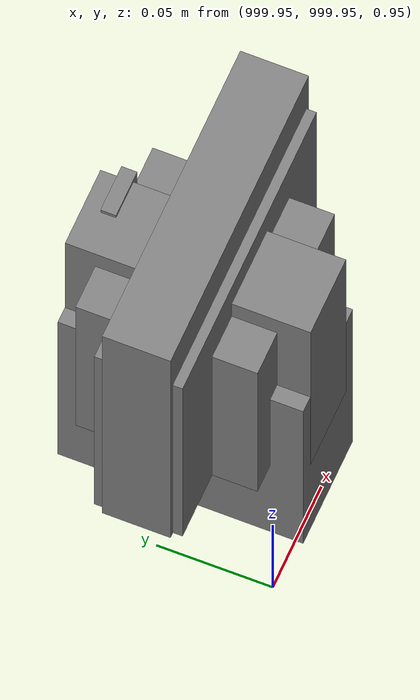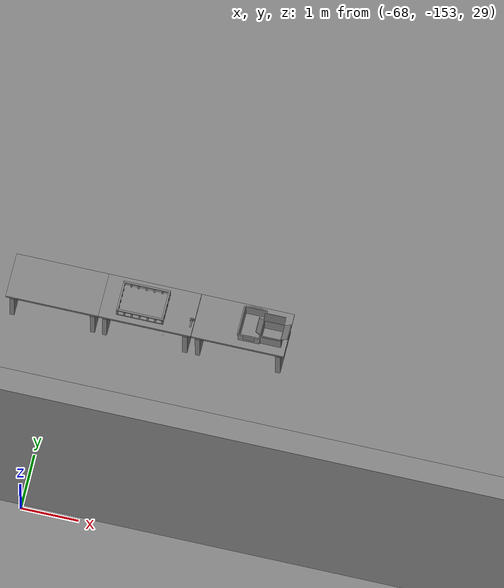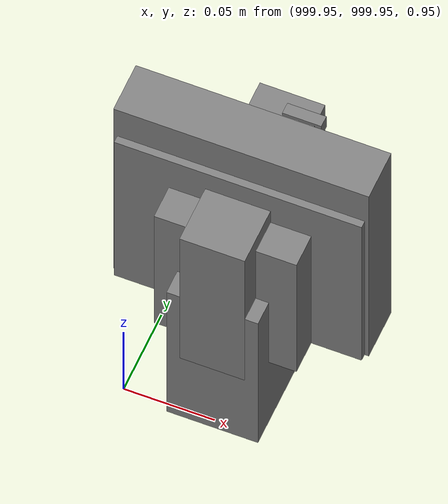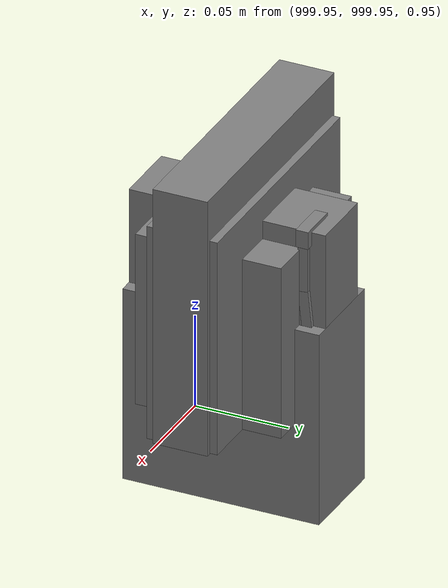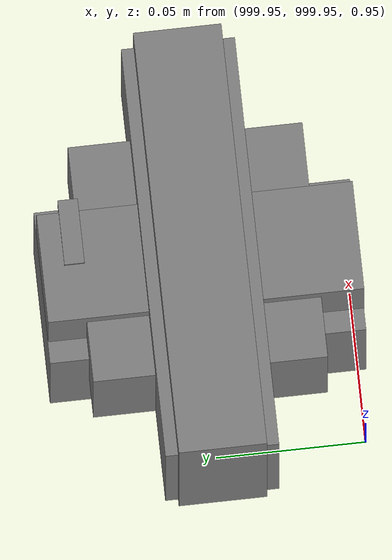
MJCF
<mujoco>
    <option gravity="0.000000000 0.000000000 -9.810000420" timestep="0.0049999999" integrator="implicitfast" density="1.225" viscosity="1.8000001e-05" noslip_iterations="10" iterations="100" sdf_iterations="50">
        <flag multiccd="disable"/>
    </option>
    <size memory="1000M"/>
    <compiler coordinate="local"/>
    <worldbody>
        <light cutoff="30" pos="0 1 1" dir="0 -1 -2"/>
        <light cutoff="30" pos="0 -1 1" dir="0 1 -2"/>
        <body pos="-64.866622925 -149.383972168 30.183746338" euler="89.999984741 89.999946594 0.000000000" name="openloong_gripper_2f85_fix_base_usda_bluebox_01">
            <geom contype="1" conaffinity="1" density="1000" type="box" material="" rgba="0.500000000 0.500000000 0.500000000 1.000000000" solimp="0.899999976 0.949999988 0.001000000" friction="1.000000000 0.005000000 0.000100000" solref="0.020000000 1.000000000" margin="0" condim="3" group="0" pos="0.276580811 0.187225342 0.000068665" quat="0.707106948 0.000077471 0.707106352 0.000077486" size="0.100000001 0.057999998 0.010000000" name="openloong_gripper_2f85_fix_base_usda_geom_E3964A8B_E461_42A1_98FA_3D1A76442B28"/>
            <geom contype="1" conaffinity="1" density="1000" type="box" material="" rgba="0.500000000 0.500000000 0.500000000 1.000000000" solimp="0.899999976 0.949999988 0.001000000" friction="1.000000000 0.005000000 0.000100000" solref="0.020000000 1.000000000" margin="0" condim="3" group="0" pos="0.000000000 0.002883911 0.000000000" quat="0.999999881 0.000000000 0.000000000 0.000000000" size="0.254000008 0.003000000 0.172000006" name="openloong_gripper_2f85_fix_base_usda_geom_11F3B5F3_7E85_4EAA_96B6_9E4A246C44F7"/>
            <geom contype="1" conaffinity="1" density="1000" type="box" material="" rgba="0.500000000 0.500000000 0.500000000 1.000000000" solimp="0.899999976 0.949999988 0.001000000" friction="1.000000000 0.005000000 0.000100000" solref="0.020000000 1.000000000" margin="0" condim="3" group="0" pos="0.000000000 0.124874115 0.173484802" quat="0.999796331 0.020176515 -0.000000015 0.000000030" size="0.259999990 0.119999997 0.007000000" name="openloong_gripper_2f85_fix_base_usda_geom_7D0F5893_3D5C_4493_A78A_AE941E304AF1"/>
            <geom contype="1" conaffinity="1" density="1000" type="box" material="" rgba="0.500000000 0.500000000 0.500000000 1.000000000" solimp="0.899999976 0.949999988 0.001000000" friction="1.000000000 0.005000000 0.000100000" solref="0.020000000 1.000000000" margin="0" condim="3" group="0" pos="0.000000000 0.124874115 -0.173469543" quat="0.999796331 -0.020176545 -0.000000015 0.000000000" size="0.259999990 0.119999997 0.007000000" name="openloong_gripper_2f85_fix_base_usda_geom_92E9CC50_40FE_4265_BC2E_9F8675C6E141"/>
            <geom contype="1" conaffinity="1" density="1000" type="box" material="" rgba="0.500000000 0.500000000 0.500000000 1.000000000" solimp="0.899999976 0.949999988 0.001000000" friction="1.000000000 0.005000000 0.000100000" solref="0.020000000 1.000000000" margin="0" condim="3" group="0" pos="0.000000000 0.214008331 0.188980103" quat="0.999912977 0.013176724 0.000000015 0.000000000" size="0.259999990 0.029999999 0.012500000" name="openloong_gripper_2f85_fix_base_usda_geom_DF20D2CA_01ED_4F2D_A35D_3CAE5561CD31"/>
            <geom contype="1" conaffinity="1" density="1000" type="box" material="" rgba="0.500000000 0.500000000 0.500000000 1.000000000" solimp="0.899999976 0.949999988 0.001000000" friction="1.000000000 0.005000000 0.000100000" solref="0.020000000 1.000000000" margin="0" condim="3" group="0" pos="-0.258361816 0.125289917 0.001876831" quat="0.702796936 -0.020792112 0.710783124 0.020769298" size="0.189999998 0.119999997 0.009000000" name="openloong_gripper_2f85_fix_base_usda_geom_CB30753A_934E_4AD7_8DDE_C140D69505C0"/>
            <geom contype="1" conaffinity="1" density="1000" type="box" material="" rgba="0.500000000 0.500000000 0.500000000 1.000000000" solimp="0.899999976 0.949999988 0.001000000" friction="1.000000000 0.005000000 0.000100000" solref="0.020000000 1.000000000" margin="0" condim="3" group="0" pos="0.000000000 0.214008331 -0.188980103" quat="0.999912977 -0.013176769 0.000000030 0.000000015" size="0.259999990 0.029999999 0.012500000" name="openloong_gripper_2f85_fix_base_usda_geom_43823370_2FF6_4112_9CD6_2BA7FB053DC5"/>
            <geom contype="1" conaffinity="1" density="1000" type="box" material="" rgba="0.500000000 0.500000000 0.500000000 1.000000000" solimp="0.899999976 0.949999988 0.001000000" friction="1.000000000 0.005000000 0.000100000" solref="0.020000000 1.000000000" margin="0" condim="3" group="0" pos="-0.276611328 0.187225342 0.000068665" quat="0.707106650 0.000077441 0.707106709 0.000077456" size="0.100000001 0.057999998 0.010000000" name="openloong_gripper_2f85_fix_base_usda_geom_FA434C79_6F6B_4A4A_BFE8_57EC68BC6F3E"/>
            <geom contype="1" conaffinity="1" density="1000" type="box" material="" rgba="0.500000000 0.500000000 0.500000000 1.000000000" solimp="0.899999976 0.949999988 0.001000000" friction="1.000000000 0.005000000 0.000100000" solref="0.020000000 1.000000000" margin="0" condim="3" group="0" pos="0.258331299 0.125289917 0.001876831" quat="0.702851415 0.018856421 0.710823774 -0.019329369" size="0.189999998 0.119999997 0.009000000" name="openloong_gripper_2f85_fix_base_usda_geom_8AC60783_0926_41F7_91D9_C39852DAAACE"/>
            <freejoint name="openloong_gripper_2f85_fix_base_usda_bluebox_01_joint"/>
            <site size="0.005000000 0.005000000 0.005000000" rgba="0.500000000 0.500000000 0.500000000 1.000000000" pos="0.000000000 0.000000000 0.000000000" quat="0.999961913 0.008726534 0.000000000 0.000000000" group="0" type="sphere" name="openloong_gripper_2f85_fix_base_usda_bluebox_01site"/>
        </body>
        <body pos="-64.496299744 -149.491867065 30.235729218" euler="0.000000000 0.000000000 89.999946594" name="openloong_gripper_2f85_fix_base_usda_cardboardbox_01">
            <geom contype="1" conaffinity="1" density="1000" type="box" material="" rgba="0.500000000 0.500000000 0.500000000 1.000000000" solimp="0.899999976 0.949999988 0.001000000" friction="1.000000000 0.005000000 0.000100000" solref="0.020000000 1.000000000" margin="0" condim="3" group="0" pos="-0.003166199 -0.004086494 0.005052090" quat="1.000000000 0.000000000 0.000000000 0.000000000" size="0.142499998 0.177500010 0.005000000" name="openloong_gripper_2f85_fix_base_usda_geom_D20B795F_AD25_481F_97FE_CF0142CB6EC0"/>
            <geom contype="1" conaffinity="1" density="1000" type="box" material="" rgba="0.500000000 0.500000000 0.500000000 1.000000000" solimp="0.899999976 0.949999988 0.001000000" friction="1.000000000 0.005000000 0.000100000" solref="0.020000000 1.000000000" margin="0" condim="3" group="0" pos="-0.003166199 0.170316696 0.150570869" quat="1.000000000 0.000000000 0.000000000 0.000000000" size="0.142499998 0.005000000 0.149999991" name="openloong_gripper_2f85_fix_base_usda_geom_A555B3F7_9CC9_47AC_9CCE_456EE5352D5D"/>
            <geom contype="1" conaffinity="1" density="1000" type="box" material="" rgba="0.500000000 0.500000000 0.500000000 1.000000000" solimp="0.899999976 0.949999988 0.001000000" friction="1.000000000 0.005000000 0.000100000" solref="0.020000000 1.000000000" margin="0" condim="3" group="0" pos="-0.147399902 -0.005307198 0.150570869" quat="1.000000000 0.000000000 0.000000000 0.000000000" size="0.005000000 0.177500010 0.149999991" name="openloong_gripper_2f85_fix_base_usda_geom_25E9380A_8A87_4BF7_A327_DB6A60CE11D9"/>
            <geom contype="1" conaffinity="1" density="1000" type="box" material="" rgba="0.500000000 0.500000000 0.500000000 1.000000000" solimp="0.899999976 0.949999988 0.001000000" friction="1.000000000 0.005000000 0.000100000" solref="0.020000000 1.000000000" margin="0" condim="3" group="0" pos="0.140275955 -0.005307198 0.150570869" quat="1.000000000 0.000000000 0.000000000 0.000000000" size="0.005000000 0.177500010 0.149999991" name="openloong_gripper_2f85_fix_base_usda_geom_0A96B058_956F_497C_9721_91CB1591E899"/>
            <geom contype="1" conaffinity="1" density="1000" type="box" material="" rgba="0.500000000 0.500000000 0.500000000 1.000000000" solimp="0.899999976 0.949999988 0.001000000" friction="1.000000000 0.005000000 0.000100000" solref="0.020000000 1.000000000" margin="0" condim="3" group="0" pos="-0.003166199 -0.181550980 0.150570869" quat="1.000000000 0.000000000 0.000000000 0.000000000" size="0.142499998 0.005000000 0.149999991" name="openloong_gripper_2f85_fix_base_usda_geom_CFB0776B_7089_4A25_A07E_93E9B6592BB3"/>
            <freejoint name="openloong_gripper_2f85_fix_base_usda_cardboardbox_01_joint"/>
            <site size="0.005000000 0.005000000 0.005000000" rgba="0.500000000 0.500000000 0.500000000 1.000000000" pos="0.000000000 0.000000000 0.000000000" quat="0.999961913 0.008726535 0.000000000 0.000000000" group="0" type="sphere" name="openloong_gripper_2f85_fix_base_usda_site_73EC35CF_A884_4043_8D75_0D9E36A3B968"/>
            <body pos="0.139160156 -0.004048347 0.301930904" euler="-179.999954224 49.383502960 179.999954224" name="openloong_gripper_2f85_fix_base_usda_A1_006">
                <geom contype="1" conaffinity="1" density="1000" type="box" material="" rgba="0.500000000 0.500000000 0.500000000 1.000000000" solimp="0.899999976 0.949999988 0.001000000" friction="1.000000000 0.005000000 0.000100000" solref="0.020000000 1.000000000" margin="0" condim="3" group="0" pos="-0.071587563 0.000009537 0.001745224" quat="0.999999881 0.000000000 0.000000000 0.000000000" size="0.071249999 0.179999992 0.002500000" name="openloong_gripper_2f85_fix_base_usda_geom_3FFF694F_89BF_4C99_8584_44E84719ADC7"/>
                <joint armature="0" stiffness="0.07" damping="0.0099999998" axis="0.000000 1.000000 0.000000" type="hinge" name="openloong_gripper_2f85_fix_base_usda_A1_006"/>
            </body>
            <body pos="-0.145902634 -0.004086494 0.301938057" euler="-180.000000000 -60.000011444 -180.000000000" name="openloong_gripper_2f85_fix_base_usda_A2_006">
                <geom contype="1" conaffinity="1" density="1000" type="box" material="" rgba="0.500000000 0.500000000 0.500000000 1.000000000" solimp="0.899999976 0.949999988 0.001000000" friction="1.000000000 0.005000000 0.000100000" solref="0.020000000 1.000000000" margin="0" condim="3" group="0" pos="0.071268082 0.000009537 0.002717972" quat="0.000002921 0.000000000 -0.000000030 0.999999881" size="0.071249999 0.179999992 0.002500000" name="openloong_gripper_2f85_fix_base_usda_geom_2D08E157_4629_4741_8BAC_7E1ACF6CC63E"/>
                <joint armature="0" stiffness="0.07" damping="0.0099999998" axis="0.000000 1.000000 0.000000" type="hinge" name="openloong_gripper_2f85_fix_base_usda_A2_006"/>
            </body>
            <body pos="-0.003385544 0.175991058 0.301930904" euler="-125.858116150 -0.000004561 0.000002331" name="openloong_gripper_2f85_fix_base_usda_B2_006">
                <geom contype="1" conaffinity="1" density="1000" type="box" material="" rgba="0.500000000 0.500000000 0.500000000 1.000000000" solimp="0.899999976 0.949999988 0.001000000" friction="1.000000000 0.005000000 0.000100000" solref="0.020000000 1.000000000" margin="0" condim="3" group="0" pos="0.000009537 -0.070939064 -0.002470016" quat="0.999614120 0.027776197 -0.000000015 0.000000030" size="0.137500003 0.064999998 0.005000000" name="openloong_gripper_2f85_fix_base_usda_geom_7B33BE10_F659_4683_BF68_59B963EE07DE"/>
                <joint armature="0" stiffness="0.07" damping="0.0099999998" axis="1.000000 0.000000 0.000000" type="hinge" name="openloong_gripper_2f85_fix_base_usda_B2_006"/>
            </body>
            <body pos="-0.003385544 -0.184140205 0.301938057" euler="147.805557251 0.000000000 0.000000000" name="openloong_gripper_2f85_fix_base_usda_B1_006">
                <geom contype="1" conaffinity="1" density="1000" type="box" material="" rgba="0.500000000 0.500000000 0.500000000 1.000000000" solimp="0.899999976 0.949999988 0.001000000" friction="1.000000000 0.005000000 0.000100000" solref="0.020000000 1.000000000" margin="0" condim="3" group="0" pos="-0.000028610 0.070202351 -0.002703667" quat="0.999614179 -0.027776167 0.000000000 0.000000000" size="0.137500003 0.064999998 0.005000000" name="openloong_gripper_2f85_fix_base_usda_geom_AC728894_39AC_43DC_9818_C0771DC11211"/>
                <joint armature="0" stiffness="0.07" damping="0.0099999998" axis="1.000000 0.000000 0.000000" type="hinge" name="openloong_gripper_2f85_fix_base_usda_B1_006"/>
            </body>
        </body>
        <body pos="-65.882858276 -149.481979370 30.229999542" euler="-64.487716675 0.000000000 0.000000000" name="openloong_gripper_2f85_fix_base_usda_Barcode">
            <geom contype="1" conaffinity="1" density="1000" type="box" material="" rgba="0.500000000 0.500000000 0.500000000 1.000000000" solimp="0.899999976 0.949999988 0.001000000" friction="1.000000000 0.005000000 0.000100000" solref="0.020000000 1.000000000" margin="0" condim="3" group="0" pos="0.000000000 0.013038635 0.001419067" quat="0.000000000 0.000000000 0.000000000 1.000000119" size="0.034000002 0.010000000 0.017999999" name="openloong_gripper_2f85_fix_base_usda_geom_59A3C8EE_04A4_41EA_B2E4_5E852092DF72"/>
            <geom contype="1" conaffinity="1" density="1000" type="box" material="" rgba="0.500000000 0.500000000 0.500000000 1.000000000" solimp="0.899999976 0.949999988 0.001000000" friction="1.000000000 0.005000000 0.000100000" solref="0.020000000 1.000000000" margin="0" condim="3" group="0" pos="0.000000000 -0.035301208 -0.007095337" quat="0.000000000 0.000000000 -0.043619365 0.999048233" size="0.028999999 0.010000000 0.020000000" name="openloong_gripper_2f85_fix_base_usda_geom_322220FF_FCE5_49F2_87DD_65B7F7885E90"/>
            <geom contype="1" conaffinity="1" density="1000" type="box" material="" rgba="0.500000000 0.500000000 0.500000000 1.000000000" solimp="0.899999976 0.949999988 0.001000000" friction="1.000000000 0.005000000 0.000100000" solref="0.020000000 1.000000000" margin="0" condim="3" group="0" pos="0.000000000 -0.043411255 -0.011749268" quat="0.922262907 0.386563420 0.000000000 0.000000000" size="0.026000001 0.010000000 0.020000000" name="openloong_gripper_2f85_fix_base_usda_geom_8449C6CB_C20E_4D01_A8E0_4579C509DD0C"/>
            <geom contype="1" conaffinity="1" density="1000" type="box" material="" rgba="0.500000000 0.500000000 0.500000000 1.000000000" solimp="0.899999976 0.949999988 0.001000000" friction="1.000000000 0.005000000 0.000100000" solref="0.020000000 1.000000000" margin="0" condim="3" group="0" pos="0.000000000 -0.016967773 -0.031860352" quat="0.000000000 0.000000000 0.000000000 1.000000119" size="0.008000000 0.010000000 0.013000000" name="openloong_gripper_2f85_fix_base_usda_geom_07D06A5B_E1B0_4E1E_ADCC_FB849DC24A0D"/>
            <geom contype="1" conaffinity="1" density="1000" type="box" material="" rgba="0.500000000 0.500000000 0.500000000 1.000000000" solimp="0.899999976 0.949999988 0.001000000" friction="1.000000000 0.005000000 0.000100000" solref="0.020000000 1.000000000" margin="0" condim="3" group="0" pos="0.000000000 -0.001869202 0.000312805" quat="0.953716993 0.300705761 0.000000000 0.000000000" size="0.032000002 0.010000000 0.018999999" name="openloong_gripper_2f85_fix_base_usda_geom_EA54DE00_38C2_47BC_88D8_43040BAC943C"/>
            <geom contype="1" conaffinity="1" density="1000" type="box" material="" rgba="0.500000000 0.500000000 0.500000000 1.000000000" solimp="0.899999976 0.949999988 0.001000000" friction="1.000000000 0.005000000 0.000100000" solref="0.020000000 1.000000000" margin="0" condim="3" group="0" pos="0.000000000 -0.019531250 -0.003173828" quat="0.953716993 0.300705761 0.000000000 0.000000000" size="0.030999999 0.010000000 0.020000000" name="openloong_gripper_2f85_fix_base_usda_geom_F967E4DC_99EE_4F1A_B52A_E9789F340247"/>
            <geom contype="1" conaffinity="1" density="1000" type="box" material="" rgba="0.500000000 0.500000000 0.500000000 1.000000000" solimp="0.899999976 0.949999988 0.001000000" friction="1.000000000 0.005000000 0.000100000" solref="0.020000000 1.000000000" margin="0" condim="3" group="0" pos="0.000000000 -0.035301208 -0.007095337" quat="0.953716993 0.300705761 0.000000000 0.000000000" size="0.028999999 0.010000000 0.020000000" name="openloong_gripper_2f85_fix_base_usda_geom_E8F3E2BC_0F92_413A_96FA_0AD86D5618C5"/>
            <geom contype="1" conaffinity="1" density="1000" type="box" material="" rgba="0.500000000 0.500000000 0.500000000 1.000000000" solimp="0.899999976 0.949999988 0.001000000" friction="1.000000000 0.005000000 0.000100000" solref="0.020000000 1.000000000" margin="0" condim="3" group="0" pos="0.000000000 -0.042617798 -0.071121216" quat="0.000000000 0.000000000 0.000000000 1.000000119" size="0.013000000 0.021000000 0.059999999" name="openloong_gripper_2f85_fix_base_usda_geom_2E63203E_E0F9_4E6A_932B_FD824053B4EE"/>
            <freejoint name="openloong_gripper_2f85_fix_base_usda_Barcode_joint"/>
            <site size="0.005000000 0.005000000 0.005000000" rgba="0.500000000 0.500000000 0.500000000 1.000000000" pos="0.000000000 0.000000000 0.000000000" quat="1.000000000 0.000000000 0.000000000 0.000000000" group="0" type="sphere" name="openloong_gripper_2f85_fix_base_usda_Barcode_site"/>
        </body>
        <body pos="-66.745018005 -149.392349243 30.184000015" euler="0.000000000 0.000000000 89.999946594" name="[22332987137827]_Basket_01">
            <geom contype="1" conaffinity="1" density="1000" type="box" material="" rgba="0.500000000 0.500000000 0.500000000 1.000000000" solimp="0.899999976 0.949999988 0.001000000" friction="1.000000000 0.005000000 0.000100000" solref="0.020000000 1.000000000" margin="0" condim="3" group="0" pos="-0.052425385 0.389207840 0.089787483" quat="0.707107008 0.000000000 0.000000000 0.707106411" size="0.014249999 0.014249999 0.059999999" name="[22332987137827]_geom_96FDB69B_671F_427C_9CB9_082EEB56CFC0"/>
            <geom contype="1" conaffinity="1" density="1000" type="box" material="" rgba="0.500000000 0.500000000 0.500000000 1.000000000" solimp="0.899999976 0.949999988 0.001000000" friction="1.000000000 0.005000000 0.000100000" solref="0.020000000 1.000000000" margin="0" condim="3" group="0" pos="0.264015198 -0.133043289 0.089787483" quat="0.707107008 0.000000000 0.000000000 0.707106411" size="0.014249999 0.014249999 0.059999999" name="[22332987137827]_geom_90F8D124_FD4F_4B51_ACBC_775EF6D0A899"/>
            <geom contype="1" conaffinity="1" density="1000" type="box" material="" rgba="0.500000000 0.500000000 0.500000000 1.000000000" solimp="0.899999976 0.949999988 0.001000000" friction="1.000000000 0.005000000 0.000100000" solref="0.020000000 1.000000000" margin="0" condim="3" group="0" pos="-0.264015198 -0.265548706 0.089793205" quat="0.707107008 0.000000000 0.000000000 0.707106411" size="0.014249999 0.014249999 0.059999999" name="[22332987137827]_geom_5700CA56_38E3_4EB8_AE94_DD9A7C90C1BD"/>
            <geom contype="1" conaffinity="1" density="1000" type="box" material="" rgba="0.500000000 0.500000000 0.500000000 1.000000000" solimp="0.899999976 0.949999988 0.001000000" friction="1.000000000 0.005000000 0.000100000" solref="0.020000000 1.000000000" margin="0" condim="3" group="0" pos="-0.160263062 -0.389322281 0.089793205" quat="0.707107008 0.000000000 0.000000000 0.707106411" size="0.014249999 0.014249999 0.059999999" name="[22332987137827]_geom_FA2DDF6E_921C_46C8_83DC_5C718C4AFDA5"/>
            <geom contype="1" conaffinity="1" density="1000" type="box" material="" rgba="0.500000000 0.500000000 0.500000000 1.000000000" solimp="0.899999976 0.949999988 0.001000000" friction="1.000000000 0.005000000 0.000100000" solref="0.020000000 1.000000000" margin="0" condim="3" group="0" pos="0.162265778 -0.389322281 0.089787483" quat="0.707107008 0.000000000 0.000000000 0.707106411" size="0.014249999 0.014249999 0.059999999" name="[22332987137827]_geom_3AB2F7ED_F0CF_4C7E_B21F_A0C7F13A738D"/>
            <geom contype="1" conaffinity="1" density="1000" type="box" material="" rgba="0.500000000 0.500000000 0.500000000 1.000000000" solimp="0.899999976 0.949999988 0.001000000" friction="1.000000000 0.005000000 0.000100000" solref="0.020000000 1.000000000" margin="0" condim="3" group="0" pos="0.264015198 0.389207840 0.089787483" quat="0.707107008 0.000000000 0.000000000 0.707106411" size="0.014249999 0.014249999 0.059999999" name="[22332987137827]_geom_3415E9EF_DD28_4F01_9C8F_F628C59FA0E6"/>
            <geom contype="1" conaffinity="1" density="1000" type="box" material="" rgba="0.500000000 0.500000000 0.500000000 1.000000000" solimp="0.899999976 0.949999988 0.001000000" friction="1.000000000 0.005000000 0.000100000" solref="0.020000000 1.000000000" margin="0" condim="3" group="0" pos="-0.264015198 -0.133043289 0.089793205" quat="0.707107008 0.000000000 0.000000000 0.707106411" size="0.014249999 0.014249999 0.059999999" name="[22332987137827]_geom_1CE74EEC_4AC3_44A5_8016_241DAB0AD882"/>
            <geom contype="1" conaffinity="1" density="1000" type="box" material="" rgba="0.500000000 0.500000000 0.500000000 1.000000000" solimp="0.899999976 0.949999988 0.001000000" friction="1.000000000 0.005000000 0.000100000" solref="0.020000000 1.000000000" margin="0" condim="3" group="0" pos="-0.264026642 0.269256592 0.089793205" quat="0.707107008 0.000000000 0.000000000 0.707106411" size="0.014249999 0.014249999 0.059999999" name="[22332987137827]_geom_34C5744D_396A_42D4_AC6D_DF6304C71F00"/>
            <geom contype="1" conaffinity="1" density="1000" type="box" material="" rgba="0.500000000 0.500000000 0.500000000 1.000000000" solimp="0.899999976 0.949999988 0.001000000" friction="1.000000000 0.005000000 0.000100000" solref="0.020000000 1.000000000" margin="0" condim="3" group="0" pos="0.054462433 0.389207840 0.089787483" quat="0.707107008 0.000000000 0.000000000 0.707106411" size="0.014249999 0.014249999 0.059999999" name="[22332987137827]_geom_ABB9ABFE_ADF4_446C_AC06_329D830C4452"/>
            <geom contype="1" conaffinity="1" density="1000" type="box" material="" rgba="0.500000000 0.500000000 0.500000000 1.000000000" solimp="0.899999976 0.949999988 0.001000000" friction="1.000000000 0.005000000 0.000100000" solref="0.020000000 1.000000000" margin="0" condim="3" group="0" pos="0.054462433 -0.389322281 0.089787483" quat="0.707107008 0.000000000 0.000000000 0.707106411" size="0.014249999 0.014249999 0.059999999" name="[22332987137827]_geom_8902F474_C59A_412B_8903_F133985208F7"/>
            <geom contype="1" conaffinity="1" density="1000" type="box" material="" rgba="0.500000000 0.500000000 0.500000000 1.000000000" solimp="0.899999976 0.949999988 0.001000000" friction="1.000000000 0.005000000 0.000100000" solref="0.020000000 1.000000000" margin="0" condim="3" group="0" pos="0.264015198 0.269256592 0.089793205" quat="0.707107008 0.000000000 0.000000000 0.707106411" size="0.014249999 0.014249999 0.059999999" name="[22332987137827]_geom_9DEC4E06_A0DF_4162_BAB6_A0042690A4D9"/>
            <geom contype="1" conaffinity="1" density="1000" type="box" material="" rgba="0.500000000 0.500000000 0.500000000 1.000000000" solimp="0.899999976 0.949999988 0.001000000" friction="1.000000000 0.005000000 0.000100000" solref="0.020000000 1.000000000" margin="0" condim="3" group="0" pos="0.264015198 -0.389322281 0.089787483" quat="0.707107008 0.000000000 0.000000000 0.707106411" size="0.014249999 0.014249999 0.059999999" name="[22332987137827]_geom_91B1B6C3_2DEF_4EDC_A1C7_D91F2D878E64"/>
            <geom contype="1" conaffinity="1" density="1000" type="box" material="" rgba="0.500000000 0.500000000 0.500000000 1.000000000" solimp="0.899999976 0.949999988 0.001000000" friction="1.000000000 0.005000000 0.000100000" solref="0.020000000 1.000000000" margin="0" condim="3" group="0" pos="0.000000000 0.000000000 0.015998840" quat="0.707107008 0.000000000 0.000000000 0.707106411" size="0.403499991 0.279000014 0.015750000" name="[22332987137827]_geom_F4DA612B_825C_4D38_8893_E65344326625"/>
            <geom contype="1" conaffinity="1" density="1000" type="box" material="" rgba="0.500000000 0.500000000 0.500000000 1.000000000" solimp="0.899999976 0.949999988 0.001000000" friction="1.000000000 0.005000000 0.000100000" solref="0.020000000 1.000000000" margin="0" condim="3" group="0" pos="0.000000000 -0.389476776 0.163619041" quat="0.707107008 0.000000000 0.000000000 0.707106411" size="0.015000000 0.277500004 0.015750000" name="[22332987137827]_geom_62B52CC9_0870_4CCC_99E4_D7DA14D969A3"/>
            <geom contype="1" conaffinity="1" density="1000" type="box" material="" rgba="0.500000000 0.500000000 0.500000000 1.000000000" solimp="0.899999976 0.949999988 0.001000000" friction="1.000000000 0.005000000 0.000100000" solref="0.020000000 1.000000000" margin="0" condim="3" group="0" pos="0.162265778 0.389207840 0.089787483" quat="0.707107008 0.000000000 0.000000000 0.707106411" size="0.014249999 0.014249999 0.059999999" name="[22332987137827]_geom_9A16AF43_FEED_404F_B8CC_007538DC6833"/>
            <geom contype="1" conaffinity="1" density="1000" type="box" material="" rgba="0.500000000 0.500000000 0.500000000 1.000000000" solimp="0.899999976 0.949999988 0.001000000" friction="1.000000000 0.005000000 0.000100000" solref="0.020000000 1.000000000" margin="0" condim="3" group="0" pos="0.000000000 0.389471054 0.163619041" quat="0.707107008 0.000000000 0.000000000 0.707106411" size="0.015000000 0.277500004 0.015750000" name="[22332987137827]_geom_148CEFA6_6DD8_416F_B766_3F9099D8D288"/>
            <geom contype="1" conaffinity="1" density="1000" type="box" material="" rgba="0.500000000 0.500000000 0.500000000 1.000000000" solimp="0.899999976 0.949999988 0.001000000" friction="1.000000000 0.005000000 0.000100000" solref="0.020000000 1.000000000" margin="0" condim="3" group="0" pos="-0.263511658 0.000000000 0.163619041" quat="0.707107008 0.000000000 0.000000000 0.707106411" size="0.403499991 0.015000000 0.015750000" name="[22332987137827]_geom_68B3116B_08FF_410D_9D9C_EAB0DB732982"/>
            <geom contype="1" conaffinity="1" density="1000" type="box" material="" rgba="0.500000000 0.500000000 0.500000000 1.000000000" solimp="0.899999976 0.949999988 0.001000000" friction="1.000000000 0.005000000 0.000100000" solref="0.020000000 1.000000000" margin="0" condim="3" group="0" pos="-0.264015198 0.141334534 0.089793205" quat="0.707107008 0.000000000 0.000000000 0.707106411" size="0.014249999 0.014249999 0.059999999" name="[22332987137827]_geom_2BAF8A80_B38B_4A47_87F7_02B43D4B88FE"/>
            <geom contype="1" conaffinity="1" density="1000" type="box" material="" rgba="0.500000000 0.500000000 0.500000000 1.000000000" solimp="0.899999976 0.949999988 0.001000000" friction="1.000000000 0.005000000 0.000100000" solref="0.020000000 1.000000000" margin="0" condim="3" group="0" pos="0.264015198 -0.265548706 0.089787483" quat="0.707107008 0.000000000 0.000000000 0.707106411" size="0.014249999 0.014249999 0.059999999" name="[22332987137827]_geom_74246BC3_44B6_441A_8422_24F15F351A29"/>
            <geom contype="1" conaffinity="1" density="1000" type="box" material="" rgba="0.500000000 0.500000000 0.500000000 1.000000000" solimp="0.899999976 0.949999988 0.001000000" friction="1.000000000 0.005000000 0.000100000" solref="0.020000000 1.000000000" margin="0" condim="3" group="0" pos="-0.160263062 0.389207840 0.089787483" quat="0.707107008 0.000000000 0.000000000 0.707106411" size="0.014249999 0.014249999 0.059999999" name="[22332987137827]_geom_365CC69C_B224_47C7_8515_A3EC440342FE"/>
            <geom contype="1" conaffinity="1" density="1000" type="box" material="" rgba="0.500000000 0.500000000 0.500000000 1.000000000" solimp="0.899999976 0.949999988 0.001000000" friction="1.000000000 0.005000000 0.000100000" solref="0.020000000 1.000000000" margin="0" condim="3" group="0" pos="-0.052425385 -0.389322281 0.089787483" quat="0.707107008 0.000000000 0.000000000 0.707106411" size="0.014249999 0.014249999 0.059999999" name="[22332987137827]_geom_C838DE25_13CF_4DB8_844E_E03969042474"/>
            <geom contype="1" conaffinity="1" density="1000" type="box" material="" rgba="0.500000000 0.500000000 0.500000000 1.000000000" solimp="0.899999976 0.949999988 0.001000000" friction="1.000000000 0.005000000 0.000100000" solref="0.020000000 1.000000000" margin="0" condim="3" group="0" pos="-0.264026642 -0.389322281 0.089793205" quat="0.707107008 0.000000000 0.000000000 0.707106411" size="0.014249999 0.014249999 0.059999999" name="[22332987137827]_geom_2D48CFF1_CA53_46BA_A40E_DB1404A383F3"/>
            <geom contype="1" conaffinity="1" density="1000" type="box" material="" rgba="0.500000000 0.500000000 0.500000000 1.000000000" solimp="0.899999976 0.949999988 0.001000000" friction="1.000000000 0.005000000 0.000100000" solref="0.020000000 1.000000000" margin="0" condim="3" group="0" pos="0.264015198 0.141334534 0.089787483" quat="0.707107008 0.000000000 0.000000000 0.707106411" size="0.014249999 0.014249999 0.059999999" name="[22332987137827]_geom_891F9FCA_E7DE_4F88_AE68_96534BE3B6A6"/>
            <geom contype="1" conaffinity="1" density="1000" type="box" material="" rgba="0.500000000 0.500000000 0.500000000 1.000000000" solimp="0.899999976 0.949999988 0.001000000" friction="1.000000000 0.005000000 0.000100000" solref="0.020000000 1.000000000" margin="0" condim="3" group="0" pos="-0.264015198 0.389207840 0.089793205" quat="0.707107008 0.000000000 0.000000000 0.707106411" size="0.014249999 0.014249999 0.059999999" name="[22332987137827]_geom_74C4BC04_A3D3_4F41_8667_30C799831533"/>
            <geom contype="1" conaffinity="1" density="1000" type="box" material="" rgba="0.500000000 0.500000000 0.500000000 1.000000000" solimp="0.899999976 0.949999988 0.001000000" friction="1.000000000 0.005000000 0.000100000" solref="0.020000000 1.000000000" margin="0" condim="3" group="0" pos="0.264015198 0.004480362 0.089787483" quat="0.707107008 0.000000000 0.000000000 0.707106411" size="0.014249999 0.014249999 0.059999999" name="[22332987137827]_geom_E5B7D018_1B22_410D_B76A_E5629CF8C8A9"/>
            <geom contype="1" conaffinity="1" density="1000" type="box" material="" rgba="0.500000000 0.500000000 0.500000000 1.000000000" solimp="0.899999976 0.949999988 0.001000000" friction="1.000000000 0.005000000 0.000100000" solref="0.020000000 1.000000000" margin="0" condim="3" group="0" pos="0.263694763 -0.000011444 0.163619041" quat="0.707107008 0.000000000 0.000000000 0.707106411" size="0.403499991 0.015000000 0.015750000" name="[22332987137827]_geom_E023E3F4_1022_4ED3_B9AB_91A4438DF4C7"/>
            <geom contype="1" conaffinity="1" density="1000" type="box" material="" rgba="0.500000000 0.500000000 0.500000000 1.000000000" solimp="0.899999976 0.949999988 0.001000000" friction="1.000000000 0.005000000 0.000100000" solref="0.020000000 1.000000000" margin="0" condim="3" group="0" pos="-0.264015198 0.004480362 0.089793205" quat="0.707107008 0.000000000 0.000000000 0.707106411" size="0.014249999 0.014249999 0.059999999" name="[22332987137827]_geom_64D83D59_9D3D_4CFD_BAC3_6F6037F1DCD5"/>
            <freejoint name="[22332987137827]_joint_B0EF1853_6942_455C_8C3D_2FEA83282778"/>
        </body>
        <body pos="0.000000000 0.000000000 0.000000000" euler="0.000000000 0.000000000 0.000000000" name="Static Objects_Static Objects">
            <geom contype="1" conaffinity="1" density="1000" type="box" material="" rgba="0.500000000 0.500000000 0.500000000 1.000000000" solimp="0.899999976 0.949999988 0.001000000" friction="1.000000000 0.005000000 0.000100000" solref="0.020000000 1.000000000" margin="0" condim="3" group="0" pos="-67.544113159 -149.365814209 29.727830887" quat="0.500000417 0.499999970 0.499999553 0.499999970" size="0.381000012 0.319999993 0.041000001" name="Static Objects_geom_EF06DA2D_7511_441E_82D2_6FD5F63A4CCB"/>
            <geom contype="1" conaffinity="1" density="1000" type="box" material="" rgba="0.500000000 0.500000000 0.500000000 1.000000000" solimp="0.899999976 0.949999988 0.001000000" friction="1.000000000 0.005000000 0.000100000" solref="0.020000000 1.000000000" margin="0" condim="3" group="0" pos="-68.239501953 -149.365814209 30.086868286" quat="0.500000417 0.499999970 0.499999553 0.499999970" size="0.370999992 0.039500002 0.745000005" name="Static Objects_geom_DDCB7141_0FAF_4BBF_9B52_B076AAC41243"/>
            <geom contype="1" conaffinity="1" density="1000" type="box" material="" rgba="0.500000000 0.500000000 0.500000000 1.000000000" solimp="0.899999976 0.949999988 0.001000000" friction="1.000000000 0.005000000 0.000100000" solref="0.020000000 1.000000000" margin="0" condim="3" group="0" pos="-68.239501953 -149.365814209 30.147235870" quat="0.500000417 0.499999970 0.499999553 0.499999970" size="0.400000006 0.022000000 0.800000012" name="Static Objects_geom_5E332BE4_0DED_4825_B52B_984C81AEB439"/>
            <geom contype="1" conaffinity="1" density="1000" type="box" material="" rgba="0.500000000 0.500000000 0.500000000 1.000000000" solimp="0.899999976 0.949999988 0.001000000" friction="1.000000000 0.005000000 0.000100000" solref="0.020000000 1.000000000" margin="0" condim="3" group="0" pos="-68.934890747 -149.365814209 29.727830887" quat="0.500000417 0.499999970 0.499999553 0.499999970" size="0.381000012 0.319999993 0.041000001" name="Static Objects_geom_095A5C00_57B2_4203_BE64_67B5B507F5D5"/>
            <geom contype="1" conaffinity="1" density="1000" type="box" material="" rgba="0.500000000 0.500000000 0.500000000 1.000000000" solimp="0.899999976 0.949999988 0.001000000" friction="1.000000000 0.005000000 0.000100000" solref="0.020000000 1.000000000" margin="0" condim="3" group="0" pos="-68.239501953 -149.365814209 29.561563492" quat="0.500000417 0.499999970 0.499999553 0.499999970" size="0.020000000 0.022000000 0.660000026" name="Static Objects_geom_4D7FE94B_A14F_4C1C_955C_D82576306AA8"/>
            <geom contype="1" conaffinity="1" density="1000" type="box" material="" rgba="0.500000000 0.500000000 0.500000000 1.000000000" solimp="0.899999976 0.949999988 0.001000000" friction="1.000000000 0.005000000 0.000100000" solref="0.020000000 1.000000000" margin="0" condim="3" group="0" pos="-65.945671082 -149.365814209 29.727830887" quat="0.500000417 0.499999970 0.499999553 0.499999970" size="0.381000012 0.319999993 0.041000001" name="Static Objects_geom_64BAA953_E582_4901_8E9D_1A8927BE9592"/>
            <geom contype="1" conaffinity="1" density="1000" type="box" material="" rgba="0.500000000 0.500000000 0.500000000 1.000000000" solimp="0.899999976 0.949999988 0.001000000" friction="1.000000000 0.005000000 0.000100000" solref="0.020000000 1.000000000" margin="0" condim="3" group="0" pos="-66.641059875 -149.365814209 30.086868286" quat="0.500000417 0.499999970 0.499999553 0.499999970" size="0.370999992 0.039500002 0.745000005" name="Static Objects_geom_08014940_64C3_4618_A4EA_F3F609C4D54B"/>
            <geom contype="1" conaffinity="1" density="1000" type="box" material="" rgba="0.500000000 0.500000000 0.500000000 1.000000000" solimp="0.899999976 0.949999988 0.001000000" friction="1.000000000 0.005000000 0.000100000" solref="0.020000000 1.000000000" margin="0" condim="3" group="0" pos="-66.641059875 -149.365814209 30.147235870" quat="0.500000417 0.499999970 0.499999553 0.499999970" size="0.400000006 0.022000000 0.800000012" name="Static Objects_geom_51489475_8184_4699_9A5D_03A32AC07A18"/>
            <geom contype="1" conaffinity="1" density="1000" type="box" material="" rgba="0.500000000 0.500000000 0.500000000 1.000000000" solimp="0.899999976 0.949999988 0.001000000" friction="1.000000000 0.005000000 0.000100000" solref="0.020000000 1.000000000" margin="0" condim="3" group="0" pos="-67.336448669 -149.365814209 29.727830887" quat="0.500000417 0.499999970 0.499999553 0.499999970" size="0.381000012 0.319999993 0.041000001" name="Static Objects_geom_3414A512_944C_44FA_A300_CE0082161D8C"/>
            <geom contype="1" conaffinity="1" density="1000" type="box" material="" rgba="0.500000000 0.500000000 0.500000000 1.000000000" solimp="0.899999976 0.949999988 0.001000000" friction="1.000000000 0.005000000 0.000100000" solref="0.020000000 1.000000000" margin="0" condim="3" group="0" pos="-66.641059875 -149.365814209 29.561563492" quat="0.500000417 0.499999970 0.499999553 0.499999970" size="0.020000000 0.022000000 0.660000026" name="Static Objects_geom_CA2392E7_546F_4105_B7B3_538ABE830B49"/>
            <geom contype="1" conaffinity="1" density="1000" type="box" material="" rgba="0.500000000 0.500000000 0.500000000 1.000000000" solimp="0.899999976 0.949999988 0.001000000" friction="1.000000000 0.005000000 0.000100000" solref="0.020000000 1.000000000" margin="0" condim="3" group="0" pos="-64.338577271 -149.365814209 29.727830887" quat="0.500000417 0.499999970 0.499999553 0.499999970" size="0.381000012 0.319999993 0.041000001" name="Static Objects_geom_936B4AB3_0841_4CF2_9B9D_EB9EFF52892C"/>
            <geom contype="1" conaffinity="1" density="1000" type="box" material="" rgba="0.500000000 0.500000000 0.500000000 1.000000000" solimp="0.899999976 0.949999988 0.001000000" friction="1.000000000 0.005000000 0.000100000" solref="0.020000000 1.000000000" margin="0" condim="3" group="0" pos="-65.033966064 -149.365814209 30.086868286" quat="0.500000417 0.499999970 0.499999553 0.499999970" size="0.370999992 0.039500002 0.745000005" name="Static Objects_geom_60D59B57_A76C_458B_80AD_4FBD1AD0F784"/>
            <geom contype="1" conaffinity="1" density="1000" type="box" material="" rgba="0.500000000 0.500000000 0.500000000 1.000000000" solimp="0.899999976 0.949999988 0.001000000" friction="1.000000000 0.005000000 0.000100000" solref="0.020000000 1.000000000" margin="0" condim="3" group="0" pos="-65.033966064 -149.365814209 30.147235870" quat="0.500000417 0.499999970 0.499999553 0.499999970" size="0.400000006 0.022000000 0.800000012" name="Static Objects_geom_AAB12C4A_F5A4_47A0_AEBC_A08A02D2C3EF"/>
            <geom contype="1" conaffinity="1" density="1000" type="box" material="" rgba="0.500000000 0.500000000 0.500000000 1.000000000" solimp="0.899999976 0.949999988 0.001000000" friction="1.000000000 0.005000000 0.000100000" solref="0.020000000 1.000000000" margin="0" condim="3" group="0" pos="-65.729354858 -149.365814209 29.727830887" quat="0.500000417 0.499999970 0.499999553 0.499999970" size="0.381000012 0.319999993 0.041000001" name="Static Objects_geom_71B7D565_96DF_4930_8104_4D4DFA988104"/>
            <geom contype="1" conaffinity="1" density="1000" type="box" material="" rgba="0.500000000 0.500000000 0.500000000 1.000000000" solimp="0.899999976 0.949999988 0.001000000" friction="1.000000000 0.005000000 0.000100000" solref="0.020000000 1.000000000" margin="0" condim="3" group="0" pos="-65.033966064 -149.365814209 29.561563492" quat="0.500000417 0.499999970 0.499999553 0.499999970" size="0.020000000 0.022000000 0.660000026" name="Static Objects_geom_E0A0DCFA_526E_4678_A3D2_A88A0859E534"/>
            <geom contype="1" conaffinity="1" density="1000" type="box" material="" rgba="0.500000000 0.500000000 0.500000000 1.000000000" solimp="0.899999976 0.949999988 0.001000000" friction="1.000000000 0.005000000 0.000100000" solref="0.020000000 1.000000000" margin="0" condim="3" group="0" pos="-61.754566193 -137.853729248 33.906845093" quat="0.707107067 0.000000000 0.000000000 0.707106471" size="0.759999990 0.759999990 4.500000000" name="Static Objects_geom_9114BE1C_09D7_49B6_AFE5_F687227D0C91"/>
            <geom contype="1" conaffinity="1" density="1000" type="box" material="" rgba="0.500000000 0.500000000 0.500000000 1.000000000" solimp="0.899999976 0.949999988 0.001000000" friction="1.000000000 0.005000000 0.000100000" solref="0.020000000 1.000000000" margin="0" condim="3" group="0" pos="-57.511135101 -144.927108765 31.707921982" quat="1.000000000 0.000000000 0.000000000 0.000000000" size="0.200000003 8.000000000 2.299999952" name="Static Objects_geom_14BAF07C_99D0_4361_B3BA_7F25D14B351A"/>
            <geom contype="1" conaffinity="1" density="1000" type="box" material="" rgba="0.500000000 0.500000000 0.500000000 1.000000000" solimp="0.899999976 0.949999988 0.001000000" friction="1.000000000 0.005000000 0.000100000" solref="0.020000000 1.000000000" margin="0" condim="3" group="0" pos="-80.517646790 -157.574050903 31.688196182" quat="0.707107067 0.000000000 0.000000000 0.707106471" size="0.600000024 0.600000024 2.299999952" name="Static Objects_geom_554059B9_D341_41FE_87AC_0A49B82FB572"/>
            <geom contype="1" conaffinity="1" density="1000" type="box" material="" rgba="0.500000000 0.500000000 0.500000000 1.000000000" solimp="0.899999976 0.949999988 0.001000000" friction="1.000000000 0.005000000 0.000100000" solref="0.020000000 1.000000000" margin="0" condim="3" group="0" pos="-80.711044312 -147.414932251 31.666158676" quat="1.000000000 0.000000000 0.000000000 0.000000000" size="0.200000003 10.000000000 2.299999952" name="Static Objects_geom_44F786C8_A3EB_4417_A379_8AD804D3E597"/>
            <geom contype="1" conaffinity="1" density="1000" type="box" material="" rgba="0.500000000 0.500000000 0.500000000 1.000000000" solimp="0.899999976 0.949999988 0.001000000" friction="1.000000000 0.005000000 0.000100000" solref="0.020000000 1.000000000" margin="0" condim="3" group="0" pos="-57.687217712 -137.434692383 31.688196182" quat="0.707107067 0.000000000 0.000000000 0.707106471" size="0.600000024 0.600000024 2.299999952" name="Static Objects_geom_46A8608D_19A2_4685_87A8_08C9790D5462"/>
            <geom contype="1" conaffinity="1" density="1000" type="box" material="" rgba="0.500000000 0.500000000 0.500000000 1.000000000" solimp="0.899999976 0.949999988 0.001000000" friction="1.000000000 0.005000000 0.000100000" solref="0.020000000 1.000000000" margin="0" condim="3" group="0" pos="-69.537033081 -140.263229370 31.714921951" quat="0.707107067 0.000000000 0.000000000 0.707106471" size="0.759999990 4.500000000 2.299999952" name="Static Objects_geom_FBC12781_01DE_4943_94CF_11A478CB2E95"/>
            <geom contype="1" conaffinity="1" density="1000" type="box" material="" rgba="0.500000000 0.500000000 0.500000000 1.000000000" solimp="0.899999976 0.949999988 0.001000000" friction="1.000000000 0.005000000 0.000100000" solref="0.020000000 1.000000000" margin="0" condim="3" group="0" pos="-80.073638916 -137.853713989 33.906845093" quat="0.707107067 0.000000000 0.000000000 0.707106471" size="0.759999990 0.759999990 4.500000000" name="Static Objects_geom_DF676C56_1309_419C_B633_66E8E49EB71D"/>
            <geom contype="1" conaffinity="1" density="1000" type="box" material="" rgba="0.500000000 0.500000000 0.500000000 1.000000000" solimp="0.899999976 0.949999988 0.001000000" friction="1.000000000 0.005000000 0.000100000" solref="0.020000000 1.000000000" margin="0" condim="3" group="0" pos="-73.406707764 -155.734664917 31.707921982" quat="1.000000000 0.000000000 0.000000000 0.000000000" size="0.200000003 3.000000000 2.299999952" name="Static Objects_geom_56B43A39_4E35_471B_A632_0A29DCA5095D"/>
            <geom contype="1" conaffinity="1" density="1000" type="box" material="" rgba="0.500000000 0.500000000 0.500000000 1.000000000" solimp="0.899999976 0.949999988 0.001000000" friction="1.000000000 0.005000000 0.000100000" solref="0.020000000 1.000000000" margin="0" condim="3" group="0" pos="-68.497543335 -137.448257446 31.707921982" quat="0.707107067 0.000000000 0.000000000 0.707106471" size="0.200000003 14.000000000 2.299999952" name="Static Objects_geom_4BACB8E4_6E4E_4CAB_9AB0_B0E9EE0ECBAA"/>
            <geom contype="1" conaffinity="1" density="1000" type="cylinder" material="" rgba="0.500000000 0.500000000 0.500000000 1.000000000" solimp="0.899999976 0.949999988 0.001000000" friction="1.000000000 0.005000000 0.000100000" solref="0.020000000 1.000000000" margin="0" condim="3" group="0" pos="-68.868522644 -142.134506226 31.711090088" quat="0.707107067 0.000000000 0.000000000 0.707106471" size="0.509999990 2.299999952 1.000000000" name="Static Objects_geom_1B53F7B4_6FC6_43BD_82FC_E2F4AF16C489"/>
            <geom contype="1" conaffinity="1" density="1000" type="plane" material="" rgba="0.500000000 0.500000000 0.500000000 1.000000000" solimp="0.899999976 0.949999988 0.001000000" friction="1.000000000 0.005000000 0.000100000" solref="0.020000000 1.000000000" margin="0" condim="3" group="0" pos="-72.873703003 -147.131927490 29.409669876" quat="1.000000000 0.000000000 0.000000000 0.000000000" size="18.000000000 14.000000000 1.000000000" name="Static Objects_geom_79CF4B7B_033D_475E_BC23_213B8B253014"/>
            <geom contype="1" conaffinity="1" density="1000" type="box" material="" rgba="0.500000000 0.500000000 0.500000000 1.000000000" solimp="0.899999976 0.949999988 0.001000000" friction="1.000000000 0.005000000 0.000100000" solref="0.020000000 1.000000000" margin="0" condim="3" group="0" pos="-79.943580627 -157.782272339 31.707921982" quat="0.707107067 0.000000000 0.000000000 0.707106471" size="0.200000003 7.000000000 2.299999952" name="Static Objects_geom_28C3A351_52F4_48CD_BF68_6FF9D67CC964"/>
            <geom contype="1" conaffinity="1" density="1000" type="box" material="" rgba="0.500000000 0.500000000 0.500000000 1.000000000" solimp="0.899999976 0.949999988 0.001000000" friction="1.000000000 0.005000000 0.000100000" solref="0.020000000 1.000000000" margin="0" condim="3" group="0" pos="-65.421028137 -152.903442383 31.707921982" quat="0.707107067 0.000000000 0.000000000 0.707106471" size="0.200000003 7.800000191 2.299999952" name="Static Objects_geom_763C1984_C8A7_46AD_99CD_8D5877F3CC9A"/>
            <geom contype="1" conaffinity="1" density="1000" type="box" material="" rgba="0.500000000 0.500000000 0.500000000 1.000000000" solimp="0.899999976 0.949999988 0.001000000" friction="1.000000000 0.005000000 0.000100000" solref="0.020000000 1.000000000" margin="0" condim="3" group="0" pos="-74.776908875 -149.964416504 31.688196182" quat="1.000000000 0.000000000 0.000000000 0.000000000" size="0.600000024 0.409999996 2.299999952" name="Static Objects_geom_8A27F18C_01E5_4599_A39E_DB1878DF69B5"/>
            <geom contype="1" conaffinity="1" density="1000" type="cylinder" material="" rgba="0.500000000 0.500000000 0.500000000 1.000000000" solimp="0.899999976 0.949999988 0.001000000" friction="1.000000000 0.005000000 0.000100000" solref="0.020000000 1.000000000" margin="0" condim="3" group="0" pos="-60.161884308 -142.134506226 31.711090088" quat="0.707107067 0.000000000 0.000000000 0.707106471" size="0.509999990 2.299999952 1.000000000" name="Static Objects_geom_581717D9_F007_4E87_819A_A74D87104ED9"/>
            <geom contype="1" conaffinity="1" density="1000" type="cylinder" material="" rgba="0.500000000 0.500000000 0.500000000 1.000000000" solimp="0.899999976 0.949999988 0.001000000" friction="1.000000000 0.005000000 0.000100000" solref="0.020000000 1.000000000" margin="0" condim="3" group="0" pos="-75.382453918 -149.963455200 31.711090088" quat="0.707107067 0.000000000 0.000000000 0.707106471" size="0.409999996 2.299999952 1.000000000" name="Static Objects_geom_5B5F3A05_D2FC_4E37_BDA8_A43C6924C8DB"/>
            <geom contype="1" conaffinity="1" density="1000" type="cylinder" material="" rgba="0.500000000 0.500000000 0.500000000 1.000000000" solimp="0.899999976 0.949999988 0.001000000" friction="1.000000000 0.005000000 0.000100000" solref="0.020000000 1.000000000" margin="0" condim="3" group="0" pos="-74.154960632 -149.963455200 31.711090088" quat="0.707107067 0.000000000 0.000000000 0.707106471" size="0.409999996 2.299999952 1.000000000" name="Static Objects_geom_B393AC5C_0E39_457C_868E_2DF56422A808"/>
            <geom contype="1" conaffinity="1" density="1000" type="cylinder" material="" rgba="0.500000000 0.500000000 0.500000000 1.000000000" solimp="0.899999976 0.949999988 0.001000000" friction="1.000000000 0.005000000 0.000100000" solref="0.020000000 1.000000000" margin="0" condim="3" group="0" pos="-77.566612244 -142.134506226 31.711090088" quat="0.707107067 0.000000000 0.000000000 0.707106471" size="0.509999990 2.299999952 1.000000000" name="Static Objects_geom_5A44986F_D950_4F65_A49C_2B882FD4C2A2"/>
        </body>
        <body pos="-65.853302002 -148.821655273 31.167364120" euler="134.964889526 -86.438896179 -16.022369385" mocap="true" name="spotlight5_SpotLight"/>
        <body pos="1000.000000000 1000.000000000 1.000000000" euler="0.000011953 0.000005123 -179.999984741" name="openloong_gripper_2f85_fix_base_usda_intel_box">
            <geom contype="1" conaffinity="1" density="1000" type="box" material="" rgba="0.500000000 0.500000000 0.500000000 1.000000000" solimp="0.899999976 0.949999988 0.001000000" friction="1.000000000 0.005000000 0.000100000" solref="0.020000000 1.000000000" margin="0" condim="3" group="0" pos="0.000000000 -0.000067139 0.000082284" quat="0.707106709 0.000000225 0.000000253 0.707106650" size="0.052800003 0.025300000 0.052800003" name="openloong_gripper_2f85_fix_base_usda_geom_0B05C0E3_8893_4946_8382_BBC30DCC85F3"/>
            <freejoint name="openloong_gripper_2f85_fix_base_usda_intel_box_joint"/>
            <site size="0.005000000 0.005000000 0.005000000" rgba="0.500000000 0.500000000 0.500000000 1.000000000" pos="0.000000000 0.000000000 0.000000000" quat="0.999961913 0.008726500 0.000000000 0.000000000" group="0" type="sphere" name="openloong_gripper_2f85_fix_base_usda_intel_boxsite"/>
        </body>
        <body pos="1000.000000000 999.999938965 1.000000000" euler="0.000000000 0.000000000 180.000000000" name="openloong_gripper_2f85_fix_base_usda_intelcore_i5">
            <geom contype="1" conaffinity="1" density="1000" type="box" material="" rgba="0.500000000 0.500000000 0.500000000 1.000000000" solimp="0.899999976 0.949999988 0.001000000" friction="1.000000000 0.005000000 0.000100000" solref="0.020000000 1.000000000" margin="0" condim="3" group="0" pos="0.000000000 0.000000000 0.051722717" quat="0.707106709 0.000000000 0.000000000 -0.707106769" size="0.052800000 0.018080002 0.052800000" name="openloong_gripper_2f85_fix_base_usda_geom_1FD8D1AE_9ED6_4119_9B73_896D9638EBB0"/>
            <freejoint name="openloong_gripper_2f85_fix_base_usda_intelcore_i5_joint"/>
            <site size="0.005000000 0.005000000 0.005000000" rgba="0.500000000 0.500000000 0.500000000 1.000000000" pos="0.000000000 0.000000000 0.000000000" quat="0.999961913 0.008726534 0.000000000 0.000000000" group="0" type="sphere" name="openloong_gripper_2f85_fix_base_usda_intelcore_i5site"/>
        </body>
        <body pos="-66.372726440 -148.874862671 31.171169281" euler="-20.136276245 -13.595752716 -113.464889526" mocap="true" name="spotlight6_SpotLight"/>
        <body pos="1000.000000000 1000.000000000 1.000000000" euler="0.000000000 0.000000000 180.000000000" name="openloong_gripper_2f85_fix_base_usda_wifi_box">
            <geom contype="1" conaffinity="1" density="1000" type="box" material="" rgba="0.500000000 0.500000000 0.500000000 1.000000000" solimp="0.899999976 0.949999988 0.001000000" friction="1.000000000 0.005000000 0.000100000" solref="0.020000000 1.000000000" margin="0" condim="3" group="0" pos="0.000000000 0.000000000 0.058978677" quat="0.000000000 0.000000047 0.000000000 1.000000000" size="0.068499997 0.018999999 0.059000000" name="openloong_gripper_2f85_fix_base_usda_geom_94A4F979_8B74_4E91_AA62_F48E7079F603"/>
            <freejoint name="openloong_gripper_2f85_fix_base_usda_wifi_box_joint"/>
            <site size="0.005000000 0.005000000 0.005000000" rgba="0.500000000 0.500000000 0.500000000 1.000000000" pos="0.000000000 0.000000000 0.000000000" quat="0.999961913 0.008726500 0.000000000 0.000000000" group="0" type="sphere" name="openloong_gripper_2f85_fix_base_usda_wifi_boxsite"/>
        </body>
        <body pos="1000.000000000 1000.000000000 1.000000000" euler="0.000000000 0.000000000 180.000000000" name="openloong_gripper_2f85_fix_base_usda_battery_01">
            <geom contype="1" conaffinity="1" density="1000" type="box" material="" rgba="0.500000000 0.500000000 0.500000000 1.000000000" solimp="0.899999976 0.949999988 0.001000000" friction="1.000000000 0.005000000 0.000100000" solref="0.020000000 1.000000000" margin="0" condim="3" group="0" pos="-0.011123657 -0.041940309 0.101691343" quat="1.000000000 0.000000000 0.000000000 0.000000000" size="0.010800000 0.003375000 0.004725000" name="openloong_gripper_2f85_fix_base_usda_geom_2E462B04_0435_466F_9BD2_7810636C7D61"/>
            <geom contype="1" conaffinity="1" density="1000" type="box" material="" rgba="0.500000000 0.500000000 0.500000000 1.000000000" solimp="0.899999976 0.949999988 0.001000000" friction="1.000000000 0.005000000 0.000100000" solref="0.020000000 1.000000000" margin="0" condim="3" group="0" pos="-0.010876465 -0.044247437 0.047066893" quat="0.998702705 -0.050920475 0.000000000 0.000000000" size="0.009450001 0.002700000 0.024975000" name="openloong_gripper_2f85_fix_base_usda_geom_2D5E6561_22BD_4203_AE94_13CBDF2F0480"/>
            <geom contype="1" conaffinity="1" density="1000" type="box" material="" rgba="0.500000000 0.500000000 0.500000000 1.000000000" solimp="0.899999976 0.949999988 0.001000000" friction="1.000000000 0.005000000 0.000100000" solref="0.020000000 1.000000000" margin="0" condim="3" group="0" pos="-0.001235962 -0.000659180 0.047381196" quat="1.000000000 0.000000000 0.000000000 0.000000000" size="0.039420001 0.039150000 0.047250003" name="openloong_gripper_2f85_fix_base_usda_geom_8ACC6980_CF10_49D3_9E4D_66D1C3363587"/>
            <geom contype="1" conaffinity="1" density="1000" type="box" material="" rgba="0.500000000 0.500000000 0.500000000 1.000000000" solimp="0.899999976 0.949999988 0.001000000" friction="1.000000000 0.005000000 0.000100000" solref="0.020000000 1.000000000" margin="0" condim="3" group="0" pos="-0.010876465 -0.039138794 0.009851727" quat="1.000000000 0.000000000 0.000000000 0.000000000" size="0.009450001 0.010800000 0.013500000" name="openloong_gripper_2f85_fix_base_usda_geom_E751B1EE_F96B_477D_9274_AC9F11C4EE8A"/>
            <geom contype="1" conaffinity="1" density="1000" type="box" material="" rgba="0.500000000 0.500000000 0.500000000 1.000000000" solimp="0.899999976 0.949999988 0.001000000" friction="1.000000000 0.005000000 0.000100000" solref="0.020000000 1.000000000" margin="0" condim="3" group="0" pos="-0.010876465 -0.041528322 0.071508206" quat="1.000000000 0.000000000 0.000000000 0.000000000" size="0.009450001 0.002700000 0.027000001" name="openloong_gripper_2f85_fix_base_usda_geom_F2F0721A_3F2D_431A_8169_565BE79AA693"/>
            <freejoint name="openloong_gripper_2f85_fix_base_usda_battery_01_joint"/>
            <site size="0.005000000 0.005000000 0.005000000" rgba="0.500000000 0.500000000 0.500000000 1.000000000" pos="0.000000000 0.000000000 0.000000000" quat="0.999961913 0.008726500 0.000000000 0.000000000" group="0" type="sphere" name="openloong_gripper_2f85_fix_base_usda_battery_01site"/>
        </body>
        <body pos="-66.105491638 -148.837707520 31.168449402" euler="-132.486663818 -30.768924713 -16.854871750" mocap="true" name="spotlight3_SpotLight"/>
        <body pos="1000.000000000 1000.000000000 1.000000000" euler="0.000000000 0.000000000 180.000000000" name="openloong_gripper_2f85_fix_base_usda_cpu_fan">
            <geom contype="1" conaffinity="1" density="1000" type="box" material="" rgba="0.500000000 0.500000000 0.500000000 1.000000000" solimp="0.899999976 0.949999988 0.001000000" friction="1.000000000 0.005000000 0.000100000" solref="0.020000000 1.000000000" margin="0" condim="3" group="0" pos="0.000000000 0.000000000 0.070034981" quat="0.000000000 0.000000000 0.000000000 1.000000000" size="0.070700005 0.014699999 0.070700005" name="openloong_gripper_2f85_fix_base_usda_geom_FA36B861_A187_4149_8D12_BFB6BA28F17A"/>
            <freejoint name="openloong_gripper_2f85_fix_base_usda_cpu_fan_joint"/>
            <site size="0.005000000 0.005000000 0.005000000" rgba="0.500000000 0.500000000 0.500000000 1.000000000" pos="0.000000000 0.000000000 0.000000000" quat="0.999961913 0.008726535 0.000000000 0.000000000" group="0" type="sphere" name="openloong_gripper_2f85_fix_base_usda_cpu_fancsite"/>
        </body>
        <body pos="-66.291030884 -149.869689941 29.018842697" euler="0.000000000 0.000000000 89.999946594" mocap="true" name="openloong_gripper_2f85_fix_base_usda_leftHandMocap"/>
        <body pos="-66.291030884 -149.869689941 29.018842697" euler="0.000000000 0.000000000 89.999946594" mocap="true" name="openloong_gripper_2f85_fix_base_usda_rightHandMocap"/>
        <body pos="-66.291030884 -149.869689941 30.218843460" euler="0.000000000 0.000000000 89.999946594" name="openloong_gripper_2f85_fix_base_usda_base_link">
            <geom contype="1" conaffinity="1" density="1000" type="mesh" material="" rgba="0.783999979 0.783999979 0.783999979 1.000000000" solimp="0.899999976 0.949999988 0.001000000" friction="1.000000000 0.005000000 0.000100000" solref="0.020000000 1.000000000" margin="0" condim="3" group="3" mesh="base_link" pos="0.000000000 0.000000000 0.000000000" quat="1.000000000 0.000000000 0.000000000 0.000000000" size="1.000000000 1.000000000 1.000000000" name="openloong_gripper_2f85_fix_base_usda__geom_7_A7EF8D25_1272_4C64_A519_C785F692EA71"/>
            <site size="0.005000000 0.005000000 0.005000000" rgba="0.500000000 0.500000000 0.500000000 1.000000000" pos="0.000000000 0.000000000 0.000000000" quat="1.000000000 0.000000000 0.000000000 0.000000000" group="0" type="sphere" name="openloong_gripper_2f85_fix_base_usda_imu"/>
            <inertial mass="22.447001" pos="-0.005664100 -0.001336700 0.238289997" diaginertia="0.374352545 0.277180195 0.220617250" quat="0.999247074 0.035235517 -0.015086859 0.006023135"/>
            <body pos="0.000000000 0.000000000 0.299997330" euler="0.000000000 0.000000000 0.000000000" name="openloong_gripper_2f85_fix_base_usda_dummy_body">
                <geom contype="1" conaffinity="1" density="1000" type="sphere" material="" rgba="0.783999979 0.783999979 0.783999979 1.000000000" solimp="0.899999976 0.949999988 0.001000000" friction="1.000000000 0.005000000 0.000100000" solref="0.020000000 1.000000000" margin="0" condim="3" group="3" pos="0.000000000 0.000000000 0.000000000" quat="1.000000000 0.000000000 0.000000000 0.000000000" size="0.010000000 0.000000000 0.000000000" name="openloong_gripper_2f85_fix_base_usda__geom_8_EF219DBD_39F2_4426_87B6_4714ED5D80E6"/>
                <joint armature="0.0099999998" stiffness="0" damping="0.1" axis="0.000000 0.000000 1.000000" type="hinge" name="openloong_gripper_2f85_fix_base_usda_dummy_joint"/>
                <site size="0.010000000 0.005000000 0.005000000" rgba="0.500000000 0.500000000 0.500000000 1.000000000" pos="0.000000000 0.000000000 0.000000000" quat="1.000000000 0.000000000 0.000000000 0.000000000" group="3" type="sphere" name="openloong_gripper_2f85_fix_base_usda_dummy_site"/>
            </body>
            <body pos="0.009002686 0.000000000 0.406400681" euler="0.000000000 0.000000000 0.000000000" name="openloong_gripper_2f85_fix_base_usda_Link_head_yaw">
                <geom contype="1" conaffinity="1" density="1000" type="mesh" material="" rgba="0.783999979 0.783999979 0.783999979 1.000000000" solimp="0.899999976 0.949999988 0.001000000" friction="1.000000000 0.005000000 0.000100000" solref="0.020000000 1.000000000" margin="0" condim="3" group="3" mesh="Link_head_yaw" pos="0.000000000 0.000000000 0.000000000" quat="1.000000000 0.000000000 0.000000000 0.000000000" size="1.000000000 1.000000000 1.000000000" name="openloong_gripper_2f85_fix_base_usda__geom_10_F839EC92_FAE3_4AA9_9133_CCF620BAE519"/>
                <inertial mass="0.84249002" pos="0.000000000 -0.002081400 0.044801001" diaginertia="0.000700588 0.000629000 0.000553812" quat="0.706933022 -0.015675601 0.015677100 0.706933022"/>
                <body pos="0.000000000 -0.034599304 0.048500061" euler="0.000000000 0.000000000 0.000000000" name="openloong_gripper_2f85_fix_base_usda_Link_head_pitch">
                    <geom contype="1" conaffinity="1" density="1000" type="mesh" material="" rgba="0.783999979 0.783999979 0.783999979 1.000000000" solimp="0.899999976 0.949999988 0.001000000" friction="1.000000000 0.005000000 0.000100000" solref="0.020000000 1.000000000" margin="0" condim="3" group="3" mesh="Link_head_pitch" pos="0.000000000 0.000000000 0.000000000" quat="1.000000000 0.000000000 0.000000000 0.000000000" size="1.000000000 1.000000000 1.000000000" name="openloong_gripper_2f85_fix_base_usda__geom_12_A4E68335_3403_4868_A47E_D7B21C908C44"/>
                    <inertial mass="1.3943" pos="0.020569000 0.033004001 0.125000000" diaginertia="0.006381400 0.006289940 0.004481460" quat="0.973390222 0.008406822 0.228157058 0.019624906"/>
                    <body pos="0.000000000 0.029998779 0.000000000" euler="0.000000000 0.000000000 0.000000000" name="openloong_gripper_2f85_fix_base_usda_neck_center_body">
                        <site size="0.010000000 0.005000000 0.005000000" rgba="0.500000000 0.500000000 0.500000000 1.000000000" pos="0.000000000 0.000000000 0.000000000" quat="1.000000000 0.000000000 0.000000000 0.000000000" group="3" type="sphere" name="openloong_gripper_2f85_fix_base_usda_neck_center_site"/>
                        <body pos="0.020004272 0.000000000 0.149999619" euler="-0.000002229 39.998176575 -90.000205994" name="openloong_gripper_2f85_fix_base_usda_camera_head">
                            <site size="0.010000000 0.005000000 0.005000000" rgba="0.500000000 0.500000000 0.500000000 1.000000000" pos="0.000000000 0.000000000 0.000000000" quat="1.000000000 0.000000000 0.000000000 0.000000000" group="3" type="sphere" name="openloong_gripper_2f85_fix_base_usda_camera_head_site"/>
                        </body>
                    </body>
                </body>
            </body>
            <body pos="0.003997803 -0.161598206 0.392200470" euler="0.000000000 0.000000000 0.000000000" name="openloong_gripper_2f85_fix_base_usda_Link_arm_r_01">
                <geom contype="1" conaffinity="1" density="1000" type="mesh" material="" rgba="0.783999979 0.783999979 0.783999979 1.000000000" solimp="0.899999976 0.949999988 0.001000000" friction="1.000000000 0.005000000 0.000100000" solref="0.020000000 1.000000000" margin="0" condim="3" group="3" mesh="Link_arm_r_01" pos="0.000000000 0.000000000 0.000000000" quat="1.000000000 0.000000000 0.000000000 0.000000000" size="1.000000000 1.000000000 1.000000000" name="openloong_gripper_2f85_fix_base_usda__geom_14_7F619AE1_0E62_4B88_BDFE_E1643E4E37B7"/>
                <joint armature="0.0099999998" stiffness="0" damping="1" axis="0.000000 -1.000000 0.000000" limited="true" range="-170.000015259 170.000015259" type="hinge" name="openloong_gripper_2f85_fix_base_usda_J_arm_r_01"/>
                <inertial mass="0.75641" pos="0.004494600 -0.038293999 -0.000001874" diaginertia="0.000842990 0.000803050 0.000587120" quat="-0.000163502 0.707098067 0.000812463 0.707115054"/>
                <body pos="-0.041992188 -0.041000366 0.000000000" euler="0.000000000 0.000000000 0.000000000" name="openloong_gripper_2f85_fix_base_usda_Link_arm_r_02">
                    <geom contype="1" conaffinity="1" density="1000" type="mesh" material="" rgba="0.783999979 0.783999979 0.783999979 1.000000000" solimp="0.899999976 0.949999988 0.001000000" friction="1.000000000 0.005000000 0.000100000" solref="0.020000000 1.000000000" margin="0" condim="3" group="3" mesh="Link_arm_r_02" pos="0.000000000 0.000000000 0.000000000" quat="1.000000000 0.000000000 0.000000000 0.000000000" size="1.000000000 1.000000000 1.000000000" name="openloong_gripper_2f85_fix_base_usda__geom_16_F0CE1E13_1F1C_4051_8DDA_61CEFDDE4682"/>
                    <joint armature="0.0099999998" stiffness="0" damping="1" axis="-1.000000 0.000000 0.000000" limited="true" range="-105.000244141 105.000244141" type="hinge" name="openloong_gripper_2f85_fix_base_usda_J_arm_r_02"/>
                    <inertial mass="0.98500001" pos="0.041999999 -0.067430697 0.000000000" diaginertia="0.002262690 0.001730990 0.001154020" quat="0.500000000 0.500000000 -0.500000000 0.500000000"/>
                    <body pos="0.041992188 -0.122596741 0.000000000" euler="0.000000000 0.000000000 0.000000000" name="openloong_gripper_2f85_fix_base_usda_Link_arm_r_03">
                        <geom contype="1" conaffinity="1" density="1000" type="mesh" material="" rgba="0.783999979 0.783999979 0.783999979 1.000000000" solimp="0.899999976 0.949999988 0.001000000" friction="1.000000000 0.005000000 0.000100000" solref="0.020000000 1.000000000" margin="0" condim="3" group="3" mesh="Link_arm_r_03" pos="0.000000000 0.000000000 0.000000000" quat="1.000000000 0.000000000 0.000000000 0.000000000" size="1.000000000 1.000000000 1.000000000" name="openloong_gripper_2f85_fix_base_usda__geom_18_6D466EEF_A5DC_466F_9B5D_A82A7D08D1B3"/>
                        <joint armature="0.0099999998" stiffness="0" damping="1" axis="0.000000 -1.000000 0.000000" limited="true" range="-170.000015259 170.000015259" type="hinge" name="openloong_gripper_2f85_fix_base_usda_J_arm_r_03"/>
                        <inertial mass="0.95899999" pos="-0.001413580 -0.164663002 0.020757901" diaginertia="0.002101340 0.002064590 0.000754802" quat="0.560480952 0.454391927 -0.443732947 0.531497955"/>
                        <body pos="0.035293579 -0.177406311 0.023998260" euler="0.000000000 0.000000000 0.000000000" name="openloong_gripper_2f85_fix_base_usda_Link_arm_r_04">
                            <geom contype="1" conaffinity="1" density="1000" type="mesh" material="" rgba="0.783999979 0.783999979 0.783999979 1.000000000" solimp="0.899999976 0.949999988 0.001000000" friction="1.000000000 0.005000000 0.000100000" solref="0.020000000 1.000000000" margin="0" condim="3" group="3" mesh="Link_arm_r_04" pos="0.000000000 0.000000000 0.000000000" quat="1.000000000 0.000000000 0.000000000 0.000000000" size="1.000000000 1.000000000 1.000000000" name="openloong_gripper_2f85_fix_base_usda__geom_20_6468E09F_1137_4162_9704_5A253617BF51"/>
                            <joint armature="0.0099999998" stiffness="0" damping="1" axis="-1.000000 0.000000 0.000000" limited="true" range="0.000000000 170.000015259" type="hinge" name="openloong_gripper_2f85_fix_base_usda_J_arm_r_04"/>
                            <inertial mass="0.60000002" pos="-0.038727000 -0.060766999 -0.021003000" diaginertia="0.001092610 0.000712422 0.000645102" quat="0.327701002 0.632602990 -0.467366993 0.523443997"/>
                            <body pos="-0.035293579 -0.103492737 -0.023998260" euler="0.000000000 0.000000000 0.000000000" name="openloong_gripper_2f85_fix_base_usda_Link_arm_r_05">
                                <geom contype="1" conaffinity="1" density="1000" type="mesh" material="" rgba="0.783999979 0.783999979 0.783999979 1.000000000" solimp="0.899999976 0.949999988 0.001000000" friction="1.000000000 0.005000000 0.000100000" solref="0.020000000 1.000000000" margin="0" condim="3" group="3" mesh="Link_arm_r_05" pos="0.000000000 0.000000000 0.000000000" quat="1.000000000 0.000000000 0.000000000 0.000000000" size="1.000000000 1.000000000 1.000000000" name="openloong_gripper_2f85_fix_base_usda__geom_22_B7088F43_6F91_4D13_BB5D_14C9B2DCB3AF"/>
                                <joint armature="0.0099999998" stiffness="0" damping="1" axis="0.000000 -1.000000 0.000000" limited="true" range="-170.000015259 170.000015259" type="hinge" name="openloong_gripper_2f85_fix_base_usda_J_arm_r_05"/>
                                <inertial mass="0.68976003" pos="0.000032712 -0.068658002 -0.000111780" diaginertia="0.002522510 0.002411100 0.000448695" quat="0.707660973 0.706543028 -0.002603360 0.002470550"/>
                                <body pos="-0.026489258 -0.196502686 0.000000000" euler="0.000000000 0.000000000 0.000000000" name="openloong_gripper_2f85_fix_base_usda_Link_arm_r_06">
                                    <geom contype="1" conaffinity="1" density="1000" type="mesh" material="" rgba="0.783999979 0.783999979 0.783999979 1.000000000" solimp="0.899999976 0.949999988 0.001000000" friction="1.000000000 0.005000000 0.000100000" solref="0.020000000 1.000000000" margin="0" condim="3" group="3" mesh="Link_arm_r_06" pos="0.000000000 0.000000000 0.000000000" quat="1.000000000 0.000000000 0.000000000 0.000000000" size="1.000000000 1.000000000 1.000000000" name="openloong_gripper_2f85_fix_base_usda__geom_24_89691443_BC85_4A04_9E15_33F7CA37AEE7"/>
                                    <joint armature="0.0099999998" stiffness="0" damping="1" axis="1.000000 0.000000 0.000000" limited="true" range="-105.000244141 105.000244141" type="hinge" name="openloong_gripper_2f85_fix_base_usda_J_arm_r_06"/>
                                    <inertial mass="0.28" pos="0.026078001 -0.000000896 0.001663700" diaginertia="0.000156930 0.000145601 0.000104979" quat="0.707080841 0.001851080 0.001883810 0.707127810"/>
                                    <body pos="0.026489258 0.000000000 0.031799316" euler="0.000000000 0.000000000 0.000000000" name="openloong_gripper_2f85_fix_base_usda_Link_arm_r_07">
                                        <geom contype="1" conaffinity="1" density="1000" type="mesh" material="" rgba="0.783999979 0.783999979 0.783999979 1.000000000" solimp="0.899999976 0.949999988 0.001000000" friction="1.000000000 0.005000000 0.000100000" solref="0.020000000 1.000000000" margin="0" condim="3" group="3" mesh="Link_arm_r_07" pos="0.000000000 0.000000000 0.000000000" quat="1.000000000 0.000000000 0.000000000 0.000000000" size="1.000000000 1.000000000 1.000000000" name="openloong_gripper_2f85_fix_base_usda__geom_26_E61ED5C9_64DF_41D8_8C5D_273343EFACD0"/>
                                        <joint armature="0.0099999998" stiffness="0" damping="1" axis="0.000000 0.000000 1.000000" limited="true" range="-60.000133514 60.000133514" type="hinge" name="openloong_gripper_2f85_fix_base_usda_J_arm_r_07"/>
                                        <inertial mass="0.61353999" pos="-0.007859000 -0.158170000 -0.027736001" diaginertia="0.003037610 0.002570910 0.000729379" quat="0.427542925 0.443532884 -0.553093910 0.560867906"/>
                                        <body pos="0.000000000 0.286994934 -0.270000458" euler="150.000350952 -0.000001649 -0.000000442" name="openloong_gripper_2f85_fix_base_usda_camera_wrist_r">
                                            <site size="0.010000000 0.005000000 0.005000000" rgba="0.500000000 0.500000000 0.500000000 1.000000000" pos="0.000000000 0.000000000 0.000000000" quat="1.000000000 0.000000000 0.000000000 0.000000000" group="3" type="sphere" name="openloong_gripper_2f85_fix_base_usda_camera_wrist_r_site"/>
                                        </body>
                                        <body pos="0.000000000 -0.220008850 -0.033002853" euler="0.000000000 0.000000000 179.999969482" name="openloong_gripper_2f85_fix_base_usda_ee_center_body_r">
                                            <site size="0.010000000 0.005000000 0.005000000" rgba="0.500000000 0.500000000 0.500000000 1.000000000" pos="0.000000000 0.000000000 0.000000000" quat="1.000000000 0.000000000 0.000000000 0.000000000" group="3" type="sphere" name="openloong_gripper_2f85_fix_base_usda_ee_center_site_r"/>
                                        </body>
                                        <body pos="0.000000000 -0.066001892 -0.031000137" euler="89.999984741 0.000000000 180.000000000" name="openloong_gripper_2f85_fix_base_usda_zbr_base_link">
                                            <geom contype="1" conaffinity="1" density="1000" type="mesh" material="" rgba="0.783999979 0.783999979 0.783999979 1.000000000" solimp="0.899999976 0.949999988 0.001000000" friction="1.000000000 0.005000000 0.000100000" solref="0.020000000 1.000000000" margin="0" condim="3" group="3" mesh="base" pos="0.000000000 0.000003815 -0.000007629" quat="1.000000000 0.000000000 0.000000000 0.000000000" size="1.000000238 1.000000238 1.000000238" name="openloong_gripper_2f85_fix_base_usda__geom_30_FFE41C8C_F931_4D87_95D5_5E2DD6A3A697"/>
                                            <inertial mass="0.77744102" pos="0.000000000 -0.000027039 0.035467502" diaginertia="0.000260285 0.000225381 0.000152708" quat="0.999998808 -0.001528488 0.000000000 0.000000000"/>
                                            <body pos="-0.030609138 0.004745484 0.065696731" euler="-89.999984741 -0.000000000 0.000000000" name="openloong_gripper_2f85_fix_base_usda_r_left_driver">
                                                <geom contype="1" conaffinity="1" density="1000" type="mesh" material="" rgba="0.783999979 0.783999979 0.783999979 1.000000000" solimp="0.899999976 0.949999988 0.001000000" friction="1.000000000 0.005000000 0.000100000" solref="0.020000000 1.000000000" margin="0" condim="3" group="3" mesh="driver" pos="0.030609138 0.054901138 -0.004699708" quat="0.707106829 0.707106709 0.000000000 -0.000000000" size="1.000000238 1.000000238 1.000000238" name="openloong_gripper_2f85_fix_base_usda__geom_32_F5079AF5_41E8_46DB_A23D_1A42A4C83927"/>
                                                <joint armature="0.0049999999" stiffness="0" damping="0.1" axis="0.000000 0.000000 1.000000" limited="true" range="0.000000000 51.566200256" type="hinge" name="openloong_gripper_2f85_fix_base_usda_r_left_driver_joint"/>
                                                <inertial mass="0.0089956298" pos="0.000000000 0.017754700 0.001073140" diaginertia="0.000001724 0.000001609 0.000000322" quat="0.681301236 0.732003212 0.000000000 0.000000000"/>
                                                <body pos="-0.031402595 0.004524232 -0.010200503" euler="0.000000000 0.000000000 180.000000000" name="openloong_gripper_2f85_fix_base_usda_r_left_coupler">
                                                    <geom contype="1" conaffinity="1" density="1000" type="mesh" material="" rgba="0.783999979 0.783999979 0.783999979 1.000000000" solimp="0.899999976 0.949999988 0.001000000" friction="1.000000000 0.005000000 0.000100000" solref="0.020000000 1.000000000" margin="0" condim="3" group="3" mesh="coupler" pos="-0.062011734 -0.050354015 0.005500795" quat="0.707106829 -0.707106709 0.000000000 -0.000000000" size="1.000000238 1.000000238 1.000000238" name="openloong_gripper_2f85_fix_base_usda__geom_34_06FDB50C_150F_4A74_96D3_6056D6FF44FA"/>
                                                    <inertial mass="0.0140974" pos="0.000000000 0.003012090 0.023217499" diaginertia="0.000004162 0.000003522 0.000000888" quat="0.705635548 -0.045590367 0.045590367 0.705635548"/>
                                                </body>
                                            </body>
                                            <body pos="-0.012695315 -0.012001040 0.072212234" euler="-89.999984741 -0.000000000 0.000000000" name="openloong_gripper_2f85_fix_base_usda_r_left_spring_link">
                                                <geom contype="1" conaffinity="1" density="1000" type="mesh" material="" rgba="0.783999979 0.783999979 0.783999979 1.000000000" solimp="0.899999976 0.949999988 0.001000000" friction="1.000000000 0.005000000 0.000100000" solref="0.020000000 1.000000000" margin="0" condim="3" group="3" mesh="spring_link" pos="0.012695315 0.061416641 0.012050631" quat="0.707106829 0.707106709 0.000000000 -0.000000000" size="1.000000238 1.000000238 1.000000238" name="openloong_gripper_2f85_fix_base_usda__geom_36_F26E6DEB_7EF8_4A9E_9D8A_E512296FDDA2"/>
                                                <joint armature="0.001" stiffness="0.050000001" damping="0.00125" axis="0.000000 0.000000 1.000000" limited="true" range="-17.000000000 51.566200256" type="hinge" name="openloong_gripper_2f85_fix_base_usda_r_left_spring_link_joint"/>
                                                <inertial mass="0.0221642" pos="-0.000000009 0.018162400 0.021265799" diaginertia="0.000008969 0.000006717 0.000002639" quat="0.663403213 -0.244737089 0.244737089 0.663403213"/>
                                                <body pos="-0.038208015 -0.042503368 0.002950669" euler="180.000000000 0.000000000 -0.002185660" name="openloong_gripper_2f85_fix_base_usda_r_left_follower">
                                                    <geom contype="1" conaffinity="1" density="1000" type="mesh" material="" rgba="0.783999979 0.783999979 0.783999979 1.000000000" solimp="0.899999976 0.949999988 0.001000000" friction="1.000000000 0.005000000 0.000100000" solref="0.020000000 1.000000000" margin="0" condim="3" group="3" mesh="tongue" pos="0.050918590 -0.103920005 -0.009099962" quat="0.707106829 -0.707106709 0.000000030 0.000000030" size="1.000000238 1.000000238 1.000000238" name="openloong_gripper_2f85_fix_base_usda__geom_40_0B0903DB_8159_4F10_A522_367DBA5A1B6B"/>
                                                    <geom contype="1" conaffinity="1" density="1000" type="mesh" material="" rgba="0.783999979 0.783999979 0.783999979 1.000000000" solimp="0.899999976 0.949999988 0.001000000" friction="1.000000000 0.005000000 0.000100000" solref="0.020000000 1.000000000" margin="0" condim="3" group="3" mesh="follower" pos="0.050918590 -0.103920005 -0.009099962" quat="0.707106829 -0.707106709 0.000000030 0.000000030" size="1.000000238 1.000000238 1.000000238" name="openloong_gripper_2f85_fix_base_usda__geom_39_2B37BEBA_31AE_4726_A22B_0F59F3F45C87"/>
                                                    <joint armature="0.001" stiffness="0" damping="0.1" axis="0.000000 0.000000 1.000000" limited="true" range="-49.999961853 51.566200256" type="hinge" name="openloong_gripper_2f85_fix_base_usda_r_left_follower"/>
                                                    <inertial mass="0.0125222" pos="0.000000000 -0.011046000 0.012478600" diaginertia="0.000002674 0.000002456 0.000000602" quat="0.986436546 0.164143041 0.000000000 0.000000000"/>
                                                    <body pos="-0.037765510 -0.103912376 -0.009099962" euler="-89.999984741 0.000000000 0.000004829" name="openloong_gripper_2f85_fix_base_usda_r_left_pad">
                                                        <geom contype="1" conaffinity="1" density="1000" type="box" material="" rgba="0.550000012 0.550000012 0.550000012 1.000000000" solimp="0.949999988 0.990000010 0.001000000" friction="0.699999988 0.005000000 0.000100000" solref="0.020000000 1.000000000" margin="0" condim="3" group="3" mass="1e-06" pos="0.043243419 0.000003815 0.119995147" quat="0.999999881 0.000000000 0.000000000 0.000000000" size="0.002000001 0.011000003 0.009375002" name="openloong_gripper_2f85_fix_base_usda_r_left_pad1_F477D6DE_4D67_437A_9912_D4737FC639EF"/>
                                                        <geom contype="1" conaffinity="1" density="1000" type="box" material="" rgba="0.449999988 0.449999988 0.449999988 1.000000000" solimp="0.949999988 0.990000010 0.001000000" friction="0.600000024 0.005000000 0.000100000" solref="0.020000000 1.000000000" margin="0" condim="3" group="3" mass="1e-06" pos="0.043243419 0.000003815 0.138748199" quat="0.999999881 0.000000000 0.000000000 0.000000000" size="0.002000001 0.011000003 0.009375002" name="openloong_gripper_2f85_fix_base_usda_r_left_pad2_55A399AF_FDC6_4BFD_97BA_11A91319B912"/>
                                                    </body>
                                                </body>
                                            </body>
                                            <body pos="0.030593880 -0.004753114 0.065696731" euler="89.999984741 0.000000000 180.000000000" name="openloong_gripper_2f85_fix_base_usda_r_right_driver">
                                                <geom contype="1" conaffinity="1" density="1000" type="mesh" material="" rgba="0.783999979 0.783999979 0.783999979 1.000000000" solimp="0.899999976 0.949999988 0.001000000" friction="1.000000000 0.005000000 0.000100000" solref="0.020000000 1.000000000" margin="0" condim="3" group="3" mesh="driver" pos="0.030593880 0.054901138 -0.004699708" quat="0.707106829 0.707106709 0.000000000 0.000000000" size="1.000000238 1.000000238 1.000000238" name="openloong_gripper_2f85_fix_base_usda__geom_42_7AB0C586_D17D_40F4_8A8D_307540E3DB16"/>
                                                <joint armature="0.0049999999" stiffness="0" damping="0.1" axis="0.000000 0.000000 1.000000" limited="true" range="0.000000000 51.566200256" type="hinge" name="openloong_gripper_2f85_fix_base_usda_r_right_driver_joint"/>
                                                <inertial mass="0.0089956298" pos="0.000000000 0.017754700 0.001073140" diaginertia="0.000001724 0.000001609 0.000000322" quat="0.681301236 0.732003212 0.000000000 0.000000000"/>
                                                <body pos="-0.031417854 0.004531861 -0.010202411" euler="0.000000000 0.000000000 180.000000000" name="openloong_gripper_2f85_fix_base_usda_r_right_coupler">
                                                    <geom contype="1" conaffinity="1" density="1000" type="mesh" material="" rgba="0.783999979 0.783999979 0.783999979 1.000000000" solimp="0.899999976 0.949999988 0.001000000" friction="1.000000000 0.005000000 0.000100000" solref="0.020000000 1.000000000" margin="0" condim="3" group="3" mesh="coupler" pos="-0.062042251 -0.050376903 0.005500795" quat="0.707106829 -0.707106709 0.000000000 0.000000000" size="1.000000238 1.000000238 1.000000238" name="openloong_gripper_2f85_fix_base_usda__geom_44_86482CED_879C_4F28_BEFB_2E4EF8374B98"/>
                                                    <inertial mass="0.0140974" pos="0.000000000 0.003012090 0.023217499" diaginertia="0.000004162 0.000003522 0.000000888" quat="0.705635548 -0.045590367 0.045590367 0.705635548"/>
                                                </body>
                                            </body>
                                            <body pos="0.012695315 0.011997226 0.072219864" euler="89.999984741 0.000000000 180.000000000" name="openloong_gripper_2f85_fix_base_usda_r_right_spring_link">
                                                <geom contype="1" conaffinity="1" density="1000" type="mesh" material="" rgba="0.783999979 0.783999979 0.783999979 1.000000000" solimp="0.899999976 0.949999988 0.001000000" friction="1.000000000 0.005000000 0.000100000" solref="0.020000000 1.000000000" margin="0" condim="3" group="3" mesh="spring_link" pos="0.012695315 0.061424270 0.012048724" quat="0.707106829 0.707106709 0.000000000 0.000000000" size="1.000000238 1.000000238 1.000000238" name="openloong_gripper_2f85_fix_base_usda__geom_46_6EFADA8B_BD7D_47A7_B2CB_B67D253B4622"/>
                                                <joint armature="0.001" stiffness="0.050000001" damping="0.00125" axis="0.000000 0.000000 1.000000" limited="true" range="-17.000000000 51.566200256" type="hinge" name="openloong_gripper_2f85_fix_base_usda_r_right_spring_link_joint"/>
                                                <inertial mass="0.0221642" pos="-0.000000009 0.018162400 0.021265799" diaginertia="0.000008969 0.000006717 0.000002639" quat="0.663403213 -0.244737089 0.244737089 0.663403213"/>
                                                <body pos="-0.038208015 -0.042495739 0.002950669" euler="180.000000000 0.000000000 0.000000000" name="openloong_gripper_2f85_fix_base_usda_r_right_follower">
                                                    <geom contype="1" conaffinity="1" density="1000" type="mesh" material="" rgba="0.783999979 0.783999979 0.783999979 1.000000000" solimp="0.899999976 0.949999988 0.001000000" friction="1.000000000 0.005000000 0.000100000" solref="0.020000000 1.000000000" margin="0" condim="3" group="3" mesh="follower" pos="0.050888073 -0.103927635 -0.009099962" quat="0.707106829 -0.707106709 0.000000000 0.000000000" size="1.000000238 1.000000238 1.000000238" name="openloong_gripper_2f85_fix_base_usda__geom_50_4B83799C_19F9_48B5_B5FB_FA86F5EB0E0C"/>
                                                    <geom contype="1" conaffinity="1" density="1000" type="mesh" material="" rgba="0.783999979 0.783999979 0.783999979 1.000000000" solimp="0.899999976 0.949999988 0.001000000" friction="1.000000000 0.005000000 0.000100000" solref="0.020000000 1.000000000" margin="0" condim="3" group="3" mesh="tongue" pos="0.050888073 -0.103927635 -0.009099962" quat="0.707106829 -0.707106709 0.000000000 0.000000000" size="1.000000238 1.000000238 1.000000238" name="openloong_gripper_2f85_fix_base_usda__geom_49_8359252A_0C47_4DB9_8ED0_BE936A1ACA8E"/>
                                                    <joint armature="0.001" stiffness="0" damping="0.1" axis="0.000000 0.000000 1.000000" limited="true" range="-49.999961853 51.566200256" type="hinge" name="openloong_gripper_2f85_fix_base_usda_r_right_follower_joint"/>
                                                    <inertial mass="0.0125222" pos="0.000000000 -0.011046000 0.012478600" diaginertia="0.000002674 0.000002456 0.000000602" quat="0.986436546 0.164143041 0.000000000 0.000000000"/>
                                                    <body pos="-0.037811287 -0.103927635 -0.009099962" euler="-89.999984741 0.000000000 0.000000000" name="openloong_gripper_2f85_fix_base_usda_r_right_pad">
                                                        <geom contype="1" conaffinity="1" density="1000" type="box" material="" rgba="0.449999988 0.449999988 0.449999988 1.000000000" solimp="0.949999988 0.990000010 0.001000000" friction="0.600000024 0.005000000 0.000100000" solref="0.020000000 1.000000000" margin="0" condim="3" group="3" mass="1e-06" pos="0.043258678 0.000000000 0.138748199" quat="1.000000000 0.000000000 0.000000000 0.000000000" size="0.002000001 0.011000003 0.009375002" name="openloong_gripper_2f85_fix_base_usda_r_right_pad2_F27D61E6_C278_4545_BE18_EF7E71CE7DC1"/>
                                                        <geom contype="1" conaffinity="1" density="1000" type="box" material="" rgba="0.550000012 0.550000012 0.550000012 1.000000000" solimp="0.949999988 0.990000010 0.001000000" friction="0.699999988 0.005000000 0.000100000" solref="0.020000000 1.000000000" margin="0" condim="3" group="3" mass="1e-06" pos="0.043258678 0.000003815 0.120002776" quat="1.000000000 0.000000000 0.000000000 0.000000000" size="0.002000001 0.011000003 0.009375002" name="openloong_gripper_2f85_fix_base_usda_r_right_pad1_89C73E1F_936C_4BF9_B16C_E6A03ACC1CCC"/>
                                                    </body>
                                                </body>
                                            </body>
                                        </body>
                                    </body>
                                </body>
                            </body>
                        </body>
                    </body>
                </body>
            </body>
            <body pos="0.003997803 0.161590576 0.392200470" euler="0.000000000 0.000000000 0.000000000" name="openloong_gripper_2f85_fix_base_usda_Link_arm_l_01">
                <geom contype="1" conaffinity="1" density="1000" type="mesh" material="" rgba="0.783999979 0.783999979 0.783999979 1.000000000" solimp="0.899999976 0.949999988 0.001000000" friction="1.000000000 0.005000000 0.000100000" solref="0.020000000 1.000000000" margin="0" condim="3" group="3" mesh="Link_arm_l_01" pos="0.000000000 0.000000000 0.000000000" quat="1.000000000 0.000000000 0.000000000 0.000000000" size="1.000000000 1.000000000 1.000000000" name="openloong_gripper_2f85_fix_base_usda__geom_52_9EB97799_2DCB_43FD_92DC_3D55C4198016"/>
                <joint armature="0.0099999998" stiffness="0" damping="1" axis="0.000000 1.000000 0.000000" limited="true" range="-170.000015259 170.000015259" type="hinge" name="openloong_gripper_2f85_fix_base_usda_J_arm_l_01"/>
                <inertial mass="0.75640601" pos="-0.004494650 0.038294200 -0.000001874" diaginertia="0.000842986 0.000803053 0.000587115" quat="-0.000812496 0.707115054 0.000163424 0.707098067"/>
                <body pos="0.042007446 0.041000366 0.000000000" euler="0.000000000 0.000000000 0.000000000" name="openloong_gripper_2f85_fix_base_usda_Link_arm_l_02">
                    <geom contype="1" conaffinity="1" density="1000" type="mesh" material="" rgba="0.783999979 0.783999979 0.783999979 1.000000000" solimp="0.899999976 0.949999988 0.001000000" friction="1.000000000 0.005000000 0.000100000" solref="0.020000000 1.000000000" margin="0" condim="3" group="3" mesh="Link_arm_l_02" pos="0.000000000 0.000000000 0.000000000" quat="1.000000000 0.000000000 0.000000000 0.000000000" size="1.000000000 1.000000000 1.000000000" name="openloong_gripper_2f85_fix_base_usda__geom_54_0A9F5581_DA2A_4AE4_8B4A_8DA17B5FCBC8"/>
                    <joint armature="0.0099999998" stiffness="0" damping="1" axis="-1.000000 0.000000 0.000000" limited="true" range="-105.000244141 105.000244141" type="hinge" name="openloong_gripper_2f85_fix_base_usda_J_arm_l_02"/>
                    <inertial mass="0.98500001" pos="-0.041999999 0.067430697 0.000000000" diaginertia="0.002262690 0.001730990 0.001154020" quat="0.500000000 0.500000000 -0.500000000 0.500000000"/>
                    <body pos="-0.042007446 0.122596741 0.000000000" euler="0.000000000 0.000000000 0.000000000" name="openloong_gripper_2f85_fix_base_usda_Link_arm_l_03">
                        <geom contype="1" conaffinity="1" density="1000" type="mesh" material="" rgba="0.783999979 0.783999979 0.783999979 1.000000000" solimp="0.899999976 0.949999988 0.001000000" friction="1.000000000 0.005000000 0.000100000" solref="0.020000000 1.000000000" margin="0" condim="3" group="3" mesh="Link_arm_l_03" pos="0.000000000 0.000000000 0.000000000" quat="1.000000000 0.000000000 0.000000000 0.000000000" size="1.000000000 1.000000000 1.000000000" name="openloong_gripper_2f85_fix_base_usda__geom_56_3EC91773_4E9A_4FD2_BA54_272B9BBD147E"/>
                        <joint armature="0.0099999998" stiffness="0" damping="1" axis="0.000000 1.000000 0.000000" limited="true" range="-170.000015259 170.000015259" type="hinge" name="openloong_gripper_2f85_fix_base_usda_J_arm_l_03"/>
                        <inertial mass="0.95899999" pos="0.001413580 0.164663002 0.020757901" diaginertia="0.002101340 0.002064590 0.000754802" quat="0.443732947 0.531497955 -0.560480952 0.454391927"/>
                        <body pos="-0.035293579 0.177406311 0.023998260" euler="0.000000000 0.000000000 0.000000000" name="openloong_gripper_2f85_fix_base_usda_Link_arm_l_04">
                            <geom contype="1" conaffinity="1" density="1000" type="mesh" material="" rgba="0.783999979 0.783999979 0.783999979 1.000000000" solimp="0.899999976 0.949999988 0.001000000" friction="1.000000000 0.005000000 0.000100000" solref="0.020000000 1.000000000" margin="0" condim="3" group="3" mesh="Link_arm_l_04" pos="0.000000000 0.000000000 0.000000000" quat="1.000000000 0.000000000 0.000000000 0.000000000" size="1.000000000 1.000000000 1.000000000" name="openloong_gripper_2f85_fix_base_usda__geom_58_E3DC51B6_62BC_4603_B161_16C910730805"/>
                            <joint armature="0.0099999998" stiffness="0" damping="1" axis="1.000000 0.000000 0.000000" limited="true" range="0.000000000 170.000015259" type="hinge" name="openloong_gripper_2f85_fix_base_usda_J_arm_l_04"/>
                            <inertial mass="0.60000002" pos="0.038727000 0.060767200 -0.021003200" diaginertia="0.001092570 0.000712419 0.000645098" quat="0.467370987 0.523440003 -0.327692002 0.632607996"/>
                            <body pos="0.035293579 0.103500366 -0.023998260" euler="0.000000000 0.000000000 0.000000000" name="openloong_gripper_2f85_fix_base_usda_Link_arm_l_05">
                                <geom contype="1" conaffinity="1" density="1000" type="mesh" material="" rgba="0.783999979 0.783999979 0.783999979 1.000000000" solimp="0.899999976 0.949999988 0.001000000" friction="1.000000000 0.005000000 0.000100000" solref="0.020000000 1.000000000" margin="0" condim="3" group="3" mesh="Link_arm_l_05" pos="0.000000000 0.000000000 0.000000000" quat="1.000000000 0.000000000 0.000000000 0.000000000" size="1.000000000 1.000000000 1.000000000" name="openloong_gripper_2f85_fix_base_usda__geom_60_83293225_B364_4B01_A1CE_068121BFD713"/>
                                <joint armature="0.0099999998" stiffness="0" damping="1" axis="0.000000 1.000000 0.000000" limited="true" range="-170.000015259 170.000015259" type="hinge" name="openloong_gripper_2f85_fix_base_usda_J_arm_l_05"/>
                                <inertial mass="0.68976003" pos="-0.000032712 0.068658002 -0.000111780" diaginertia="0.002522510 0.002411100 0.000448695" quat="0.706543028 0.707660973 0.002470550 -0.002603360"/>
                                <body pos="0.026504517 0.196495056 0.000000000" euler="0.000000000 0.000000000 0.000000000" name="openloong_gripper_2f85_fix_base_usda_Link_arm_l_06">
                                    <geom contype="1" conaffinity="1" density="1000" type="mesh" material="" rgba="0.783999979 0.783999979 0.783999979 1.000000000" solimp="0.899999976 0.949999988 0.001000000" friction="1.000000000 0.005000000 0.000100000" solref="0.020000000 1.000000000" margin="0" condim="3" group="3" mesh="Link_arm_l_06" pos="0.000000000 0.000000000 0.000000000" quat="1.000000000 0.000000000 0.000000000 0.000000000" size="1.000000000 1.000000000 1.000000000" name="openloong_gripper_2f85_fix_base_usda__geom_62_B5692085_7128_4EB4_95DA_028B5D26C5A9"/>
                                    <joint armature="0.0099999998" stiffness="0" damping="1" axis="-1.000000 0.000000 0.000000" limited="true" range="-105.000244141 105.000244141" type="hinge" name="openloong_gripper_2f85_fix_base_usda_J_arm_l_06"/>
                                    <inertial mass="0.28" pos="-0.026077701 0.000000896 0.001663730" diaginertia="0.000156927 0.000145598 0.000104981" quat="0.707080841 -0.001851280 -0.001884020 0.707127810"/>
                                    <body pos="-0.026504517 0.000000000 0.031799316" euler="0.000000000 0.000000000 0.000000000" name="openloong_gripper_2f85_fix_base_usda_Link_arm_l_07">
                                        <geom contype="1" conaffinity="1" density="1000" type="mesh" material="" rgba="0.783999979 0.783999979 0.783999979 1.000000000" solimp="0.899999976 0.949999988 0.001000000" friction="1.000000000 0.005000000 0.000100000" solref="0.020000000 1.000000000" margin="0" condim="3" group="3" mesh="Link_arm_l_07" pos="0.000000000 0.000000000 0.000000000" quat="1.000000000 0.000000000 0.000000000 0.000000000" size="1.000000000 1.000000000 1.000000000" name="openloong_gripper_2f85_fix_base_usda__geom_64_3D0C01C8_5059_4919_8A2A_5664ADB6F68C"/>
                                        <joint armature="0.0099999998" stiffness="0" damping="1" axis="0.000000 0.000000 1.000000" limited="true" range="-60.000133514 60.000133514" type="hinge" name="openloong_gripper_2f85_fix_base_usda_J_arm_l_07"/>
                                        <inertial mass="0.61353999" pos="-0.007787200 0.157049999 -0.027733000" diaginertia="0.003037200 0.002570420 0.000729374" quat="0.443562120 0.427539080 -0.560871124 0.553070128"/>
                                        <body pos="0.000000000 -0.286994934 -0.270000458" euler="-150.000350952 0.000001955 179.976669312" name="openloong_gripper_2f85_fix_base_usda_camera_wrist_l">
                                            <site size="0.010000000 0.005000000 0.005000000" rgba="0.500000000 0.500000000 0.500000000 1.000000000" pos="0.000000000 0.000000000 0.000000000" quat="1.000000000 0.000000000 0.000000000 0.000000000" group="3" type="sphere" name="openloong_gripper_2f85_fix_base_usda_camera_wrist_l_site"/>
                                        </body>
                                        <body pos="0.000000000 0.220008850 -0.033002853" euler="0.000000000 0.000000000 0.000000000" name="openloong_gripper_2f85_fix_base_usda_ee_center_body">
                                            <site size="0.010000000 0.005000000 0.005000000" rgba="0.500000000 0.500000000 0.500000000 1.000000000" pos="0.000000000 0.000000000 0.000000000" quat="1.000000000 0.000000000 0.000000000 0.000000000" group="3" type="sphere" name="openloong_gripper_2f85_fix_base_usda_ee_center_site"/>
                                        </body>
                                        <body pos="0.000000000 0.066009521 -0.031000137" euler="-90.000007629 0.000000000 0.000000000" name="openloong_gripper_2f85_fix_base_usda_zbll_base_link">
                                            <geom contype="1" conaffinity="1" density="1000" type="mesh" material="" rgba="0.783999979 0.783999979 0.783999979 1.000000000" solimp="0.899999976 0.949999988 0.001000000" friction="1.000000000 0.005000000 0.000100000" solref="0.020000000 1.000000000" margin="0" condim="3" group="3" mesh="base" pos="0.000000000 0.000000000 0.000000000" quat="1.000000000 0.000000000 0.000000000 0.000000000" size="1.000000000 1.000000000 1.000000000" name="openloong_gripper_2f85_fix_base_usda__geom_68_661F4CBE_A2A1_46A6_BC7F_92396E9445AA"/>
                                            <inertial mass="0.77744102" pos="0.000000000 -0.000027039 0.035467502" diaginertia="0.000260285 0.000225381 0.000152708" quat="0.999998808 -0.001528488 0.000000000 0.000000000"/>
                                            <body pos="-0.030578613 0.004755020 0.065696716" euler="-89.999984741 0.000000000 0.000000000" name="openloong_gripper_2f85_fix_base_usda_l_left_driver">
                                                <geom contype="1" conaffinity="1" density="1000" type="mesh" material="" rgba="0.783999979 0.783999979 0.783999979 1.000000000" solimp="0.899999976 0.949999988 0.001000000" friction="1.000000000 0.005000000 0.000100000" solref="0.020000000 1.000000000" margin="0" condim="3" group="3" mesh="driver" pos="0.030609131 0.054901123 -0.004699707" quat="0.707106829 0.707106709 0.000000000 0.000000000" size="1.000000000 1.000000000 1.000000000" name="openloong_gripper_2f85_fix_base_usda__geom_70_34140888_8E34_4B62_8F0C_07B5A5A420C1"/>
                                                <joint armature="0.0049999999" stiffness="0" damping="0.1" axis="0.000000 0.000000 1.000000" limited="true" range="0.000000000 51.566200256" type="hinge" name="openloong_gripper_2f85_fix_base_usda_l_left_driver_joint"/>
                                                <inertial mass="0.0089956298" pos="0.000000000 0.017754700 0.001073140" diaginertia="0.000001724 0.000001609 0.000000322" quat="0.681301236 0.732003212 0.000000000 0.000000000"/>
                                                <body pos="-0.031402588 0.004531860 -0.010200500" euler="0.000000000 0.000000000 180.000000000" name="openloong_gripper_2f85_fix_base_usda_l_left_coupler">
                                                    <geom contype="1" conaffinity="1" density="1000" type="mesh" material="" rgba="0.783999979 0.783999979 0.783999979 1.000000000" solimp="0.899999976 0.949999988 0.001000000" friction="1.000000000 0.005000000 0.000100000" solref="0.020000000 1.000000000" margin="0" condim="3" group="3" mesh="coupler" pos="-0.062042236 -0.050369263 0.005500793" quat="0.707106829 -0.707106709 0.000000000 0.000000000" size="1.000000000 1.000000000 1.000000000" name="openloong_gripper_2f85_fix_base_usda__geom_72_5BB36005_AA0D_4F6C_87D2_14835DFA767A"/>
                                                    <inertial mass="0.0140974" pos="0.000000000 0.003012090 0.023217499" diaginertia="0.000004162 0.000003522 0.000000888" quat="0.705635548 -0.045590367 0.045590367 0.705635548"/>
                                                </body>
                                            </body>
                                            <body pos="-0.012680054 -0.011987686 0.072204590" euler="-89.999984741 0.000000000 0.000000000" name="openloong_gripper_2f85_fix_base_usda_l_left_spring_link">
                                                <geom contype="1" conaffinity="1" density="1000" type="mesh" material="" rgba="0.783999979 0.783999979 0.783999979 1.000000000" solimp="0.899999976 0.949999988 0.001000000" friction="1.000000000 0.005000000 0.000100000" solref="0.020000000 1.000000000" margin="0" condim="3" group="3" mesh="spring_link" pos="0.012725830 0.061431885 0.012050629" quat="0.707106829 0.707106709 0.000000000 0.000000000" size="1.000000000 1.000000000 1.000000000" name="openloong_gripper_2f85_fix_base_usda__geom_74_3AAA337D_3786_4D83_B343_B71E93CE9600"/>
                                                <joint armature="0.001" stiffness="0.050000001" damping="0.00125" axis="0.000000 0.000000 1.000000" limited="true" range="-17.000000000 51.566200256" type="hinge" name="openloong_gripper_2f85_fix_base_usda_l_left_spring_link_joint"/>
                                                <inertial mass="0.0221642" pos="-0.000000009 0.018162400 0.021265799" diaginertia="0.000008969 0.000006717 0.000002639" quat="0.663403213 -0.244737089 0.244737089 0.663403213"/>
                                                <body pos="-0.038192749 -0.042495728 0.002950668" euler="180.000000000 0.000000000 -0.002185660" name="openloong_gripper_2f85_fix_base_usda_l_left_follower">
                                                    <geom contype="1" conaffinity="1" density="1000" type="mesh" material="" rgba="0.783999979 0.783999979 0.783999979 1.000000000" solimp="0.899999976 0.949999988 0.001000000" friction="1.000000000 0.005000000 0.000100000" solref="0.020000000 1.000000000" margin="0" condim="3" group="3" mesh="follower" pos="0.050933838 -0.103919983 -0.009098053" quat="0.707106829 -0.707106650 0.000000000 -0.000000030" size="1.000000000 1.000000000 1.000000000" name="openloong_gripper_2f85_fix_base_usda__geom_77_8A17B1B8_B8C7_4817_8EE8_54B1E70964F4"/>
                                                    <geom contype="1" conaffinity="1" density="1000" type="mesh" material="" rgba="0.783999979 0.783999979 0.783999979 1.000000000" solimp="0.899999976 0.949999988 0.001000000" friction="1.000000000 0.005000000 0.000100000" solref="0.020000000 1.000000000" margin="0" condim="3" group="3" mesh="tongue" pos="0.050933838 -0.103919983 -0.009098053" quat="0.707106829 -0.707106650 0.000000000 -0.000000030" size="1.000000000 1.000000000 1.000000000" name="openloong_gripper_2f85_fix_base_usda__geom_78_AE5BC764_7C4C_40C1_B57E_8B0D14535BF6"/>
                                                    <joint armature="0.001" stiffness="0" damping="0.1" axis="0.000000 0.000000 1.000000" limited="true" range="-49.999961853 51.566200256" type="hinge" name="openloong_gripper_2f85_fix_base_usda_l_left_follower"/>
                                                    <inertial mass="0.0125222" pos="0.000000000 -0.011046000 0.012478600" diaginertia="0.000002674 0.000002456 0.000000602" quat="0.986436546 0.164143041 0.000000000 0.000000000"/>
                                                    <body pos="-0.037780762 -0.103919983 -0.009098053" euler="-89.999977112 0.000002415 -0.000002415" name="openloong_gripper_2f85_fix_base_usda_l_left_pad">
                                                        <geom contype="1" conaffinity="1" density="1000" type="box" material="" rgba="0.550000012 0.550000012 0.550000012 1.000000000" solimp="0.949999988 0.990000010 0.001000000" friction="0.699999988 0.005000000 0.000100000" solref="0.020000000 1.000000000" margin="0" condim="3" group="3" mass="1e-06" pos="0.043273926 0.000009537 0.119995117" quat="0.999999881 0.000000000 0.000000000 0.000000000" size="0.002000000 0.011000000 0.009375000" name="openloong_gripper_2f85_fix_base_usda_l_left_pad1_B9A1EB55_8B77_404A_8CCC_FCEC0E185097"/>
                                                        <geom contype="1" conaffinity="1" density="1000" type="box" material="" rgba="0.449999988 0.449999988 0.449999988 1.000000000" solimp="0.949999988 0.990000010 0.001000000" friction="0.600000024 0.005000000 0.000100000" solref="0.020000000 1.000000000" margin="0" condim="3" group="3" mass="1e-06" pos="0.043273926 0.000017166 0.138732910" quat="0.999999881 0.000000000 0.000000000 0.000000000" size="0.002000000 0.011000000 0.009375000" name="openloong_gripper_2f85_fix_base_usda_l_left_pad2_48E89343_D976_46A6_AF63_727A424C5FBD"/>
                                                    </body>
                                                </body>
                                            </body>
                                            <body pos="0.030609131 -0.004739761 0.065689087" euler="89.999984741 0.000000000 180.000000000" name="openloong_gripper_2f85_fix_base_usda_l_right_driver">
                                                <geom contype="1" conaffinity="1" density="1000" type="mesh" material="" rgba="0.783999979 0.783999979 0.783999979 1.000000000" solimp="0.899999976 0.949999988 0.001000000" friction="1.000000000 0.005000000 0.000100000" solref="0.020000000 1.000000000" margin="0" condim="3" group="3" mesh="driver" pos="0.030593872 0.054901123 -0.004697800" quat="0.707106829 0.707106709 0.000000000 0.000000000" size="1.000000000 1.000000000 1.000000000" name="openloong_gripper_2f85_fix_base_usda__geom_80_EE393C75_C0C8_4F6B_8996_955D2E0ECDC4"/>
                                                <joint armature="0.0049999999" stiffness="0" damping="0.1" axis="0.000000 0.000000 1.000000" limited="true" range="0.000000000 51.566200256" type="hinge" name="openloong_gripper_2f85_fix_base_usda_l_right_driver_joint"/>
                                                <inertial mass="0.0089956298" pos="0.000000000 0.017754700 0.001073140" diaginertia="0.000001724 0.000001609 0.000000322" quat="0.681301236 0.732003212 0.000000000 0.000000000"/>
                                                <body pos="-0.031433105 0.004531860 -0.010198593" euler="0.000000000 0.000000000 180.000000000" name="openloong_gripper_2f85_fix_base_usda_l_right_coupler">
                                                    <geom contype="1" conaffinity="1" density="1000" type="mesh" material="" rgba="0.783999979 0.783999979 0.783999979 1.000000000" solimp="0.899999976 0.949999988 0.001000000" friction="1.000000000 0.005000000 0.000100000" solref="0.020000000 1.000000000" margin="0" condim="3" group="3" mesh="coupler" pos="-0.062011719 -0.050369263 0.005502701" quat="0.707106829 -0.707106709 0.000000000 0.000000000" size="1.000000000 1.000000000 1.000000000" name="openloong_gripper_2f85_fix_base_usda__geom_82_9682B98F_145D_4FEA_901B_1C8DF379B309"/>
                                                    <inertial mass="0.0140974" pos="0.000000000 0.003012090 0.023217499" diaginertia="0.000004162 0.000003522 0.000000888" quat="0.705635548 -0.045590367 0.045590367 0.705635548"/>
                                                </body>
                                            </body>
                                            <body pos="0.012710571 0.012010574 0.072204590" euler="89.999984741 0.000000000 180.000000000" name="openloong_gripper_2f85_fix_base_usda_l_right_spring_link">
                                                <geom contype="1" conaffinity="1" density="1000" type="mesh" material="" rgba="0.783999979 0.783999979 0.783999979 1.000000000" solimp="0.899999976 0.949999988 0.001000000" friction="1.000000000 0.005000000 0.000100000" solref="0.020000000 1.000000000" margin="0" condim="3" group="3" mesh="spring_link" pos="0.012695312 0.061416626 0.012052536" quat="0.707106829 0.707106709 0.000000000 0.000000000" size="1.000000000 1.000000000 1.000000000" name="openloong_gripper_2f85_fix_base_usda__geom_84_B63738D3_3E27_4028_916C_030718D9C968"/>
                                                <joint armature="0.001" stiffness="0.050000001" damping="0.00125" axis="0.000000 0.000000 1.000000" limited="true" range="-17.000000000 51.566200256" type="hinge" name="openloong_gripper_2f85_fix_base_usda_l_right_spring_link_joint"/>
                                                <inertial mass="0.0221642" pos="-0.000000009 0.018162400 0.021265799" diaginertia="0.000008969 0.000006717 0.000002639" quat="0.663403213 -0.244737089 0.244737089 0.663403213"/>
                                                <body pos="-0.038208008 -0.042503357 0.002952576" euler="180.000000000 0.000000000 0.000000000" name="openloong_gripper_2f85_fix_base_usda_l_right_follower">
                                                    <geom contype="1" conaffinity="1" density="1000" type="mesh" material="" rgba="0.783999979 0.783999979 0.783999979 1.000000000" solimp="0.899999976 0.949999988 0.001000000" friction="1.000000000 0.005000000 0.000100000" solref="0.020000000 1.000000000" margin="0" condim="3" group="3" mesh="tongue" pos="0.050903320 -0.103919983 -0.009099960" quat="0.707106829 -0.707106709 -0.000000030 -0.000000030" size="1.000000000 1.000000000 1.000000000" name="openloong_gripper_2f85_fix_base_usda__geom_87_B2E7AC00_4040_46E9_902A_65EA07D19F22"/>
                                                    <geom contype="1" conaffinity="1" density="1000" type="mesh" material="" rgba="0.783999979 0.783999979 0.783999979 1.000000000" solimp="0.899999976 0.949999988 0.001000000" friction="1.000000000 0.005000000 0.000100000" solref="0.020000000 1.000000000" margin="0" condim="3" group="3" mesh="follower" pos="0.050903320 -0.103919983 -0.009099960" quat="0.707106829 -0.707106709 -0.000000030 -0.000000030" size="1.000000000 1.000000000 1.000000000" name="openloong_gripper_2f85_fix_base_usda__geom_88_99E9A202_C4C0_4791_A014_61880471BF1E"/>
                                                    <joint armature="0.001" stiffness="0" damping="0.1" axis="0.000000 0.000000 1.000000" limited="true" range="-49.999961853 51.566200256" type="hinge" name="openloong_gripper_2f85_fix_base_usda_l_right_follower_joint"/>
                                                    <inertial mass="0.0125222" pos="0.000000000 -0.011046000 0.012478600" diaginertia="0.000002674 0.000002456 0.000000602" quat="0.986436546 0.164143041 0.000000000 0.000000000"/>
                                                    <body pos="-0.037796021 -0.103912354 -0.009099960" euler="-89.999984741 -0.000000000 -0.000004830" name="openloong_gripper_2f85_fix_base_usda_l_right_pad">
                                                        <geom contype="1" conaffinity="1" density="1000" type="box" material="" rgba="0.550000012 0.550000012 0.550000012 1.000000000" solimp="0.949999988 0.990000010 0.001000000" friction="0.699999988 0.005000000 0.000100000" solref="0.020000000 1.000000000" margin="0" condim="3" group="3" mass="1e-06" pos="0.043258667 0.000000000 0.119995117" quat="1.000000000 0.000000000 0.000000000 0.000000000" size="0.002000000 0.011000000 0.009375000" name="openloong_gripper_2f85_fix_base_usda_l_right_pad1_40083094_29C4_401E_A694_DCF678A0A9F6"/>
                                                        <geom contype="1" conaffinity="1" density="1000" type="box" material="" rgba="0.449999988 0.449999988 0.449999988 1.000000000" solimp="0.949999988 0.990000010 0.001000000" friction="0.600000024 0.005000000 0.000100000" solref="0.020000000 1.000000000" margin="0" condim="3" group="3" mass="1e-06" pos="0.043258667 0.000000000 0.138748169" quat="1.000000000 0.000000000 0.000000000 0.000000000" size="0.002000000 0.011000000 0.009375000" name="openloong_gripper_2f85_fix_base_usda_l_right_pad2_1B30D94C_FA72_4123_95CC_AFBCAE8DBAFC"/>
                                                    </body>
                                                </body>
                                            </body>
                                        </body>
                                    </body>
                                </body>
                            </body>
                        </body>
                    </body>
                </body>
            </body>
            <body pos="0.000000000 -0.065246582 0.000000000" euler="0.000000000 0.000000000 0.000000000" name="openloong_gripper_2f85_fix_base_usda_Link_waist_pitch">
                <geom contype="1" conaffinity="1" density="1000" type="mesh" material="" rgba="0.783999979 0.783999979 0.783999979 1.000000000" solimp="0.899999976 0.949999988 0.001000000" friction="1.000000000 0.005000000 0.000100000" solref="0.020000000 1.000000000" margin="0" condim="3" group="3" mesh="Link_waist_pitch" pos="0.000000000 0.000000000 0.000000000" quat="1.000000000 0.000000000 0.000000000 0.000000000" size="1.000000000 1.000000000 1.000000000" name="openloong_gripper_2f85_fix_base_usda__geom_90_8051D7AB_B748_4A74_A5F4_FDF67DB65A3E"/>
                <inertial mass="2.6963999" pos="-0.000734960 0.049924999 -0.000029695" diaginertia="0.006190620 0.005201250 0.004737120" quat="0.524125040 0.474713057 -0.522095084 0.476820052"/>
                <body pos="-0.063995361 0.065498352 0.000000000" euler="0.000000000 0.000000000 0.000000000" name="openloong_gripper_2f85_fix_base_usda_Link_waist_roll">
                    <geom contype="1" conaffinity="1" density="1000" type="mesh" material="" rgba="0.783999979 0.783999979 0.783999979 1.000000000" solimp="0.899999976 0.949999988 0.001000000" friction="1.000000000 0.005000000 0.000100000" solref="0.020000000 1.000000000" margin="0" condim="3" group="3" mesh="Link_waist_roll" pos="0.000000000 0.000000000 0.000000000" quat="1.000000000 0.000000000 0.000000000 0.000000000" size="1.000000000 1.000000000 1.000000000" name="openloong_gripper_2f85_fix_base_usda__geom_92_CFFF52AB_30B6_4B17_98C9_12215F86E72C"/>
                    <inertial mass="2.9806001" pos="-0.003742400 -0.001000000 -0.016856000" diaginertia="0.018825000 0.017314700 0.005873970" quat="0.576995134 0.408750087 0.408750087 0.576995134"/>
                    <body pos="0.067520142 0.000000000 -0.097999573" euler="0.000000000 0.000000000 0.000000000" name="openloong_gripper_2f85_fix_base_usda_Link_waist_yaw">
                        <geom contype="1" conaffinity="1" density="1000" type="mesh" material="" rgba="0.783999979 0.783999979 0.783999979 1.000000000" solimp="0.899999976 0.949999988 0.001000000" friction="1.000000000 0.005000000 0.000100000" solref="0.020000000 1.000000000" margin="0" condim="3" group="3" mesh="Link_waist_yaw" pos="0.000000000 0.000000000 0.000000000" quat="1.000000000 0.000000000 0.000000000 0.000000000" size="1.000000000 1.000000000 1.000000000" name="openloong_gripper_2f85_fix_base_usda__geom_94_ACFFC2F2_B28D_4A68_B537_9F54FD7A7A43"/>
                        <inertial mass="7.3587999" pos="-0.096171997 -0.001000000 -0.057836000" diaginertia="0.109522998 0.089752100 0.032765999" quat="0.571972013 0.571972013 -0.415749997 0.415749997"/>
                        <body pos="-0.087493896 -0.120002747 -0.069000244" euler="0.000000000 0.000000000 0.000000000" name="openloong_gripper_2f85_fix_base_usda_Link_hip_r_roll">
                            <geom contype="1" conaffinity="1" density="1000" type="mesh" material="" rgba="0.783999979 0.783999979 0.783999979 1.000000000" solimp="0.899999976 0.949999988 0.001000000" friction="1.000000000 0.005000000 0.000100000" solref="0.020000000 1.000000000" margin="0" condim="3" group="3" mesh="Link_hip_r_roll" pos="0.000000000 0.000000000 0.000000000" quat="1.000000000 0.000000000 0.000000000 0.000000000" size="1.000000000 1.000000000 1.000000000" name="openloong_gripper_2f85_fix_base_usda__geom_96_DF00A06B_3540_484B_8C61_234812C53822"/>
                            <inertial mass="2.4333999" pos="0.075724997 -0.001061600 0.016590999" diaginertia="0.004506770 0.003996270 0.003606060" quat="0.357336968 0.610613942 0.606069922 0.363510966"/>
                            <body pos="0.082229614 -0.000999451 -0.009998322" euler="0.000000000 0.000000000 0.000000000" name="openloong_gripper_2f85_fix_base_usda_Link_hip_r_yaw">
                                <geom contype="1" conaffinity="1" density="1000" type="mesh" material="" rgba="0.783999979 0.783999979 0.783999979 1.000000000" solimp="0.899999976 0.949999988 0.001000000" friction="1.000000000 0.005000000 0.000100000" solref="0.020000000 1.000000000" margin="0" condim="3" group="3" mesh="Link_hip_r_yaw" pos="0.000000000 0.000000000 0.000000000" quat="1.000000000 0.000000000 0.000000000 0.000000000" size="1.000000000 1.000000000 1.000000000" name="openloong_gripper_2f85_fix_base_usda__geom_98_4FE27A33_6181_42D8_93CC_A39AA82A23A8"/>
                                <inertial mass="3.4303" pos="-0.000000031 -0.007135600 -0.100630000" diaginertia="0.008090100 0.007736500 0.006631600" quat="0.706536055 0.028403703 -0.028403703 0.706536055"/>
                                <body pos="0.000000000 0.036750793 -0.105501175" euler="0.000000000 0.000000000 0.000000000" name="openloong_gripper_2f85_fix_base_usda_Link_hip_r_pitch">
                                    <geom contype="1" conaffinity="1" density="1000" type="mesh" material="" rgba="0.783999979 0.783999979 0.783999979 1.000000000" solimp="0.899999976 0.949999988 0.001000000" friction="1.000000000 0.005000000 0.000100000" solref="0.020000000 1.000000000" margin="0" condim="3" group="3" mesh="Link_hip_r_pitch" pos="0.000000000 0.000000000 0.000000000" quat="1.000000000 0.000000000 0.000000000 0.000000000" size="1.000000000 1.000000000 1.000000000" name="openloong_gripper_2f85_fix_base_usda__geom_100_D834B2E1_CC25_4D1D_A6AA_4FB5462C4B96"/>
                                    <inertial mass="5.2378001" pos="0.001085600 -0.054970000 -0.145349994" diaginertia="0.043490201 0.037812300 0.015138500" quat="0.999495864 -0.015916798 0.013696698 0.023812896"/>
                                    <body pos="0.000000000 -0.011253357 -0.400001526" euler="0.000000000 0.000000000 0.000000000" name="openloong_gripper_2f85_fix_base_usda_Link_knee_r_pitch">
                                        <geom contype="1" conaffinity="1" density="1000" type="mesh" material="" rgba="0.783999979 0.783999979 0.783999979 1.000000000" solimp="0.899999976 0.949999988 0.001000000" friction="1.000000000 0.005000000 0.000100000" solref="0.020000000 1.000000000" margin="0" condim="3" group="3" mesh="Link_knee_r_pitch" pos="0.000000000 0.000000000 0.000000000" quat="1.000000000 0.000000000 0.000000000 0.000000000" size="1.000000000 1.000000000 1.000000000" name="openloong_gripper_2f85_fix_base_usda__geom_102_3D50164D_9AEE_4D4E_9BCE_38E2B2329A97"/>
                                        <inertial mass="2.9775" pos="-0.009642500 0.000002934 -0.136010006" diaginertia="0.024215899 0.023851801 0.002284610" quat="0.782037616 -0.003061678 0.016178992 0.623013675"/>
                                        <body pos="0.000000000 0.000000000 -0.386999130" euler="0.000000000 0.000000000 0.000000000" name="openloong_gripper_2f85_fix_base_usda_Link_ankle_r_pitch">
                                            <geom contype="1" conaffinity="1" density="1000" type="mesh" material="" rgba="0.783999979 0.783999979 0.783999979 1.000000000" solimp="0.899999976 0.949999988 0.001000000" friction="1.000000000 0.005000000 0.000100000" solref="0.020000000 1.000000000" margin="0" condim="3" group="3" mesh="Link_ankle_r_pitch" pos="0.000000000 0.000000000 0.000000000" quat="1.000000000 0.000000000 0.000000000 0.000000000" size="1.000000000 1.000000000 1.000000000" name="openloong_gripper_2f85_fix_base_usda__geom_104_5C68B648_91FF_493C_BF7D_5696FFB5663D"/>
                                            <inertial mass="0.10145" pos="-0.000000000 -0.000000127 -0.000000025" diaginertia="0.000027175 0.000026565 0.000006112" quat="0.707106829 0.707106829 0.000000000 0.000000000"/>
                                            <body pos="0.000000000 0.000000000 0.000000000" euler="0.000000000 0.000000000 0.000000000" name="openloong_gripper_2f85_fix_base_usda_Link_ankle_r_roll">
                                                <geom contype="1" conaffinity="1" density="1000" type="box" material="" rgba="1.000000000 0.000000000 0.000000000 0.000000000" solimp="0.899999976 0.949999988 0.001000000" friction="1.000000000 0.005000000 0.000100000" solref="0.020000000 1.000000000" margin="0" condim="3" group="3" pos="0.047515869 0.000083923 -0.026544571" quat="1.000000000 0.000000000 0.000000000 0.000000000" size="0.122500002 0.039999999 0.043499999" name="openloong_gripper_2f85_fix_base_usda__geom_106_65C73820_AE45_4DEF_8EC7_9B7BFC61C104"/>
                                                <site size="0.123000003 0.041000001 0.044000000" rgba="0.000000000 1.000000000 0.000000000 0.000000000" pos="0.047504615 0.000082667 -0.026545310" quat="1.000000000 0.000000000 0.000000000 0.000000000" group="3" type="box" name="openloong_gripper_2f85_fix_base_usda_rf-tc"/>
                                                <inertial mass="0.75229001" pos="0.041078001 -0.000000089 -0.043908998" diaginertia="0.003659370 0.003646500 0.000416828" quat="0.000000000 0.677034914 0.000000000 0.735950947"/>
                                            </body>
                                        </body>
                                    </body>
                                </body>
                            </body>
                        </body>
                        <body pos="-0.087493896 0.120002747 -0.069000244" euler="0.000000000 0.000000000 0.000000000" name="openloong_gripper_2f85_fix_base_usda_Link_hip_l_roll">
                            <geom contype="1" conaffinity="1" density="1000" type="mesh" material="" rgba="0.783999979 0.783999979 0.783999979 1.000000000" solimp="0.899999976 0.949999988 0.001000000" friction="1.000000000 0.005000000 0.000100000" solref="0.020000000 1.000000000" margin="0" condim="3" group="3" mesh="Link_hip_l_roll" pos="0.000000000 0.000000000 0.000000000" quat="1.000000000 0.000000000 0.000000000 0.000000000" size="1.000000000 1.000000000 1.000000000" name="openloong_gripper_2f85_fix_base_usda__geom_108_79231C59_3456_48C1_9CCC_0CD46AFBF9C5"/>
                            <inertial mass="2.4333999" pos="0.075724997 -0.000938430 0.016590999" diaginertia="0.004257030 0.003974770 0.003377790" quat="0.411751240 0.573205352 0.583885372 0.401216239"/>
                            <body pos="0.082229614 -0.000999451 -0.009998322" euler="0.000000000 0.000000000 0.000000000" name="openloong_gripper_2f85_fix_base_usda_Link_hip_l_yaw">
                                <geom contype="1" conaffinity="1" density="1000" type="mesh" material="" rgba="0.783999979 0.783999979 0.783999979 1.000000000" solimp="0.899999976 0.949999988 0.001000000" friction="1.000000000 0.005000000 0.000100000" solref="0.020000000 1.000000000" margin="0" condim="3" group="3" mesh="Link_hip_l_yaw" pos="0.000000000 0.000000000 0.000000000" quat="1.000000000 0.000000000 0.000000000 0.000000000" size="1.000000000 1.000000000 1.000000000" name="openloong_gripper_2f85_fix_base_usda__geom_110_1A5C0B44_7232_46EF_898F_32A14114CC1F"/>
                                <inertial mass="3.4303999" pos="-0.000000032 0.007135800 -0.100630000" diaginertia="0.008090100 0.007736500 0.006631500" quat="0.706536174 -0.028401807 0.028401807 0.706536174"/>
                                <body pos="0.000000000 -0.036758423 -0.105501175" euler="0.000000000 0.000000000 0.000000000" name="openloong_gripper_2f85_fix_base_usda_Link_hip_l_pitch">
                                    <geom contype="1" conaffinity="1" density="1000" type="mesh" material="" rgba="0.783999979 0.783999979 0.783999979 1.000000000" solimp="0.899999976 0.949999988 0.001000000" friction="1.000000000 0.005000000 0.000100000" solref="0.020000000 1.000000000" margin="0" condim="3" group="3" mesh="Link_hip_l_pitch" pos="0.000000000 0.000000000 0.000000000" quat="1.000000000 0.000000000 0.000000000 0.000000000" size="1.000000000 1.000000000 1.000000000" name="openloong_gripper_2f85_fix_base_usda__geom_112_54380277_96AA_44CA_9340_65FE5769EF56"/>
                                    <inertial mass="5.2378001" pos="0.001085600 0.054970000 -0.145349994" diaginertia="0.043490201 0.037812300 0.015138500" quat="0.999495745 0.015916597 0.013696796 -0.023821594"/>
                                    <body pos="0.000000000 0.011260986 -0.400001526" euler="0.000000000 0.000000000 0.000000000" name="openloong_gripper_2f85_fix_base_usda_Link_knee_l_pitch">
                                        <geom contype="1" conaffinity="1" density="1000" type="mesh" material="" rgba="0.783999979 0.783999979 0.783999979 1.000000000" solimp="0.899999976 0.949999988 0.001000000" friction="1.000000000 0.005000000 0.000100000" solref="0.020000000 1.000000000" margin="0" condim="3" group="3" mesh="Link_knee_l_pitch" pos="0.000000000 0.000000000 0.000000000" quat="1.000000000 0.000000000 0.000000000 0.000000000" size="1.000000000 1.000000000 1.000000000" name="openloong_gripper_2f85_fix_base_usda__geom_114_59ECF2E0_B5AE_4C1F_80E1_B40F8F33C503"/>
                                        <inertial mass="2.9775" pos="-0.009642500 -0.000002868 -0.136010006" diaginertia="0.024214899 0.023850800 0.002284610" quat="0.623014212 0.016178306 -0.003060011 0.782037318"/>
                                        <body pos="0.000000000 0.000000000 -0.386999130" euler="0.000000000 0.000000000 0.000000000" name="openloong_gripper_2f85_fix_base_usda_Link_ankle_l_pitch">
                                            <geom contype="1" conaffinity="1" density="1000" type="mesh" material="" rgba="0.783999979 0.783999979 0.783999979 1.000000000" solimp="0.899999976 0.949999988 0.001000000" friction="1.000000000 0.005000000 0.000100000" solref="0.020000000 1.000000000" margin="0" condim="3" group="3" mesh="Link_ankle_l_pitch" pos="0.000000000 0.000000000 0.000000000" quat="1.000000000 0.000000000 0.000000000 0.000000000" size="1.000000000 1.000000000 1.000000000" name="openloong_gripper_2f85_fix_base_usda__geom_116_3BDA4AB7_0028_44B2_918F_D8A2FCAB85D9"/>
                                            <inertial mass="0.10145" pos="-0.000000000 0.000000127 0.000000067" diaginertia="0.000027175 0.000026565 0.000006112" quat="0.707106829 0.707106829 0.000000000 0.000000000"/>
                                            <body pos="0.000000000 0.000000000 0.000000000" euler="0.000000000 0.000000000 0.000000000" name="openloong_gripper_2f85_fix_base_usda_Link_ankle_l_roll">
                                                <geom contype="1" conaffinity="1" density="1000" type="box" material="" rgba="1.000000000 0.000000000 0.000000000 0.000000000" solimp="0.899999976 0.949999988 0.001000000" friction="1.000000000 0.005000000 0.000100000" solref="0.020000000 1.000000000" margin="0" condim="3" group="3" pos="0.047515869 0.001220703 -0.027221680" quat="1.000000000 0.000000000 0.000000000 0.000000000" size="0.122500002 0.040199999 0.044199999" name="openloong_gripper_2f85_fix_base_usda__geom_118_1DE7DA73_61E6_4A75_9C2E_B9CE927049DC"/>
                                                <site size="0.123000003 0.041000001 0.045000002" rgba="0.000000000 1.000000000 0.000000000 0.000000000" pos="0.047499999 0.001220864 -0.027223988" quat="1.000000000 0.000000000 0.000000000 0.000000000" group="3" type="box" name="openloong_gripper_2f85_fix_base_usda_lf-tc"/>
                                                <inertial mass="0.75228798" pos="0.041076999 -0.000000029 -0.043908998" diaginertia="0.003659370 0.003646500 0.000416828" quat="0.000000000 0.677034914 0.000000000 0.735950947"/>
                                            </body>
                                        </body>
                                    </body>
                                </body>
                            </body>
                        </body>
                    </body>
                </body>
            </body>
        </body>
    </worldbody>
    <tendon>
        <fixed name="openloong_gripper_2f85_fix_base_usda_l_split">
            <joint joint="openloong_gripper_2f85_fix_base_usda_l_right_driver_joint" coef="0.48500001"/>
            <joint joint="openloong_gripper_2f85_fix_base_usda_l_left_driver_joint" coef="0.48500001"/>
        </fixed>
        <fixed name="openloong_gripper_2f85_fix_base_usda_r_split">
            <joint joint="openloong_gripper_2f85_fix_base_usda_r_right_driver_joint" coef="0.48500001"/>
            <joint joint="openloong_gripper_2f85_fix_base_usda_r_left_driver_joint" coef="0.48500001"/>
        </fixed>
    </tendon>
    <actuator>
        <position ctrllimited="true" ctrlrange="-2.96706 2.96706" forcelimited="true" forcerange="-80 80" joint="openloong_gripper_2f85_fix_base_usda_J_arm_l_01" kp="200" kv="20" name="openloong_gripper_2f85_fix_base_usda_P_arm_l_01"/>
        <position ctrllimited="true" ctrlrange="-1.8326 1.8326" forcelimited="true" forcerange="-80 80" joint="openloong_gripper_2f85_fix_base_usda_J_arm_l_02" kp="200" kv="20" name="openloong_gripper_2f85_fix_base_usda_P_arm_l_02"/>
        <position ctrllimited="true" ctrlrange="-2.96706 2.96706" forcelimited="true" forcerange="-48 48" joint="openloong_gripper_2f85_fix_base_usda_J_arm_l_03" kp="200" kv="20" name="openloong_gripper_2f85_fix_base_usda_P_arm_l_03"/>
        <position ctrllimited="true" ctrlrange="0 2.96706" forcelimited="true" forcerange="-48 48" joint="openloong_gripper_2f85_fix_base_usda_J_arm_l_04" kp="200" kv="20" name="openloong_gripper_2f85_fix_base_usda_P_arm_l_04"/>
        <position ctrllimited="true" ctrlrange="-2.96706 2.96706" forcelimited="true" forcerange="-12.4 12.4" joint="openloong_gripper_2f85_fix_base_usda_J_arm_l_05" kp="200" kv="20" name="openloong_gripper_2f85_fix_base_usda_P_arm_l_05"/>
        <position ctrllimited="true" ctrlrange="-1.8326 1.8326" forcelimited="true" forcerange="-12.4 12.4" joint="openloong_gripper_2f85_fix_base_usda_J_arm_l_06" kp="200" kv="20" name="openloong_gripper_2f85_fix_base_usda_P_arm_l_06"/>
        <position ctrllimited="true" ctrlrange="-1.0472 1.0472" forcelimited="true" forcerange="-12.4 12.4" joint="openloong_gripper_2f85_fix_base_usda_J_arm_l_07" kp="200" kv="20" name="openloong_gripper_2f85_fix_base_usda_P_arm_l_07"/>
        <motor ctrllimited="true" ctrlrange="-80 80" gear="1" joint="openloong_gripper_2f85_fix_base_usda_J_arm_l_01" name="openloong_gripper_2f85_fix_base_usda_M_arm_l_01"/>
        <motor ctrllimited="true" ctrlrange="-80 80" gear="1" joint="openloong_gripper_2f85_fix_base_usda_J_arm_l_02" name="openloong_gripper_2f85_fix_base_usda_M_arm_l_02"/>
        <motor ctrllimited="true" ctrlrange="-48 48" gear="1" joint="openloong_gripper_2f85_fix_base_usda_J_arm_l_03" name="openloong_gripper_2f85_fix_base_usda_M_arm_l_03"/>
        <motor ctrllimited="true" ctrlrange="-48 48" gear="1" joint="openloong_gripper_2f85_fix_base_usda_J_arm_l_04" name="openloong_gripper_2f85_fix_base_usda_M_arm_l_04"/>
        <motor ctrllimited="true" ctrlrange="-12.4 12.4" gear="1" joint="openloong_gripper_2f85_fix_base_usda_J_arm_l_05" name="openloong_gripper_2f85_fix_base_usda_M_arm_l_05"/>
        <motor ctrllimited="true" ctrlrange="-12.4 12.4" gear="1" joint="openloong_gripper_2f85_fix_base_usda_J_arm_l_06" name="openloong_gripper_2f85_fix_base_usda_M_arm_l_06"/>
        <motor ctrllimited="true" ctrlrange="-12.4 12.4" gear="1" joint="openloong_gripper_2f85_fix_base_usda_J_arm_l_07" name="openloong_gripper_2f85_fix_base_usda_M_arm_l_07"/>
        <position ctrllimited="true" ctrlrange="-2.96706 2.96706" forcelimited="true" forcerange="-80 80" joint="openloong_gripper_2f85_fix_base_usda_J_arm_r_01" kp="200" kv="20" name="openloong_gripper_2f85_fix_base_usda_P_arm_r_01"/>
        <position ctrllimited="true" ctrlrange="-1.8326 1.8326" forcelimited="true" forcerange="-80 80" joint="openloong_gripper_2f85_fix_base_usda_J_arm_r_02" kp="200" kv="20" name="openloong_gripper_2f85_fix_base_usda_P_arm_r_02"/>
        <position ctrllimited="true" ctrlrange="-2.96706 2.96706" forcelimited="true" forcerange="-48 48" joint="openloong_gripper_2f85_fix_base_usda_J_arm_r_03" kp="200" kv="20" name="openloong_gripper_2f85_fix_base_usda_P_arm_r_03"/>
        <position ctrllimited="true" ctrlrange="0 2.96706" forcelimited="true" forcerange="-48 48" joint="openloong_gripper_2f85_fix_base_usda_J_arm_r_04" kp="200" kv="20" name="openloong_gripper_2f85_fix_base_usda_P_arm_r_04"/>
        <position ctrllimited="true" ctrlrange="-2.96706 2.96706" forcelimited="true" forcerange="-12.4 12.4" joint="openloong_gripper_2f85_fix_base_usda_J_arm_r_05" kp="200" kv="20" name="openloong_gripper_2f85_fix_base_usda_P_arm_r_05"/>
        <position ctrllimited="true" ctrlrange="-1.8326 1.8326" forcelimited="true" forcerange="-12.4 12.4" joint="openloong_gripper_2f85_fix_base_usda_J_arm_r_06" kp="200" kv="20" name="openloong_gripper_2f85_fix_base_usda_P_arm_r_06"/>
        <position ctrllimited="true" ctrlrange="-1.0472 1.0472" forcelimited="true" forcerange="-12.4 12.4" joint="openloong_gripper_2f85_fix_base_usda_J_arm_r_07" kp="200" kv="20" name="openloong_gripper_2f85_fix_base_usda_P_arm_r_07"/>
        <motor ctrllimited="true" ctrlrange="-80 80" gear="1" joint="openloong_gripper_2f85_fix_base_usda_J_arm_r_01" name="openloong_gripper_2f85_fix_base_usda_M_arm_r_01"/>
        <motor ctrllimited="true" ctrlrange="-80 80" gear="1" joint="openloong_gripper_2f85_fix_base_usda_J_arm_r_02" name="openloong_gripper_2f85_fix_base_usda_M_arm_r_02"/>
        <motor ctrllimited="true" ctrlrange="-48 48" gear="1" joint="openloong_gripper_2f85_fix_base_usda_J_arm_r_03" name="openloong_gripper_2f85_fix_base_usda_M_arm_r_03"/>
        <motor ctrllimited="true" ctrlrange="-48 48" gear="1" joint="openloong_gripper_2f85_fix_base_usda_J_arm_r_04" name="openloong_gripper_2f85_fix_base_usda_M_arm_r_04"/>
        <motor ctrllimited="true" ctrlrange="-12.4 12.4" gear="1" joint="openloong_gripper_2f85_fix_base_usda_J_arm_r_05" name="openloong_gripper_2f85_fix_base_usda_M_arm_r_05"/>
        <motor ctrllimited="true" ctrlrange="-12.4 12.4" gear="1" joint="openloong_gripper_2f85_fix_base_usda_J_arm_r_06" name="openloong_gripper_2f85_fix_base_usda_M_arm_r_06"/>
        <motor ctrllimited="true" ctrlrange="-12.4 12.4" gear="1" joint="openloong_gripper_2f85_fix_base_usda_J_arm_r_07" name="openloong_gripper_2f85_fix_base_usda_M_arm_r_07"/>
        <general biasprm="0 -100 -10" biastype="affine" ctrlrange="0 255" forcerange="-5 5" gainprm="0.3137255 0 0" name="openloong_gripper_2f85_fix_base_usda_l_fingers_actuator" tendon="openloong_gripper_2f85_fix_base_usda_l_split"/>
        <general biasprm="0 -100 -10" biastype="affine" ctrlrange="0 255" forcerange="-5 5" gainprm="0.3137255 0 0" name="openloong_gripper_2f85_fix_base_usda_r_fingers_actuator" tendon="openloong_gripper_2f85_fix_base_usda_r_split"/>
    </actuator>
    <contact>
        <exclude body1="openloong_gripper_2f85_fix_base_usda_base_link" body2="openloong_gripper_2f85_fix_base_usda_Link_head_yaw"/>
        <exclude body1="openloong_gripper_2f85_fix_base_usda_base_link" body2="openloong_gripper_2f85_fix_base_usda_dummy_body"/>
        <exclude body1="openloong_gripper_2f85_fix_base_usda_base_link" body2="openloong_gripper_2f85_fix_base_usda_Link_waist_roll"/>
        <exclude body1="openloong_gripper_2f85_fix_base_usda_base_link" body2="openloong_gripper_2f85_fix_base_usda_Link_arm_r_01"/>
        <exclude body1="openloong_gripper_2f85_fix_base_usda_base_link" body2="openloong_gripper_2f85_fix_base_usda_Link_waist_pitch"/>
        <exclude body1="openloong_gripper_2f85_fix_base_usda_base_link" body2="openloong_gripper_2f85_fix_base_usda_Link_head_pitch"/>
        <exclude body1="openloong_gripper_2f85_fix_base_usda_base_link" body2="openloong_gripper_2f85_fix_base_usda_Link_arm_l_01"/>
        <exclude body1="openloong_gripper_2f85_fix_base_usda_Link_arm_l_01" body2="openloong_gripper_2f85_fix_base_usda_Link_arm_l_02"/>
        <exclude body1="openloong_gripper_2f85_fix_base_usda_Link_arm_l_02" body2="openloong_gripper_2f85_fix_base_usda_Link_arm_l_03"/>
        <exclude body1="openloong_gripper_2f85_fix_base_usda_Link_arm_l_03" body2="openloong_gripper_2f85_fix_base_usda_Link_arm_l_04"/>
        <exclude body1="openloong_gripper_2f85_fix_base_usda_Link_arm_l_04" body2="openloong_gripper_2f85_fix_base_usda_Link_arm_l_05"/>
        <exclude body1="openloong_gripper_2f85_fix_base_usda_Link_arm_l_05" body2="openloong_gripper_2f85_fix_base_usda_Link_arm_l_06"/>
        <exclude body1="openloong_gripper_2f85_fix_base_usda_Link_arm_l_05" body2="openloong_gripper_2f85_fix_base_usda_Link_arm_l_07"/>
        <exclude body1="openloong_gripper_2f85_fix_base_usda_Link_arm_l_06" body2="openloong_gripper_2f85_fix_base_usda_Link_arm_l_07"/>
        <exclude body1="openloong_gripper_2f85_fix_base_usda_zbll_base_link" body2="openloong_gripper_2f85_fix_base_usda_l_left_driver"/>
        <exclude body1="openloong_gripper_2f85_fix_base_usda_zbll_base_link" body2="openloong_gripper_2f85_fix_base_usda_l_right_spring_link"/>
        <exclude body1="openloong_gripper_2f85_fix_base_usda_zbll_base_link" body2="openloong_gripper_2f85_fix_base_usda_l_left_spring_link"/>
        <exclude body1="openloong_gripper_2f85_fix_base_usda_zbll_base_link" body2="openloong_gripper_2f85_fix_base_usda_l_right_driver"/>
        <exclude body1="openloong_gripper_2f85_fix_base_usda_l_left_coupler" body2="openloong_gripper_2f85_fix_base_usda_l_left_follower"/>
        <exclude body1="openloong_gripper_2f85_fix_base_usda_l_right_coupler" body2="openloong_gripper_2f85_fix_base_usda_l_right_follower"/>
        <exclude body1="openloong_gripper_2f85_fix_base_usda_Link_waist_pitch" body2="openloong_gripper_2f85_fix_base_usda_Link_waist_roll"/>
        <exclude body1="openloong_gripper_2f85_fix_base_usda_Link_waist_roll" body2="openloong_gripper_2f85_fix_base_usda_Link_waist_yaw"/>
        <exclude body1="openloong_gripper_2f85_fix_base_usda_Link_waist_yaw" body2="openloong_gripper_2f85_fix_base_usda_Link_hip_r_yaw"/>
        <exclude body1="openloong_gripper_2f85_fix_base_usda_Link_waist_yaw" body2="openloong_gripper_2f85_fix_base_usda_Link_hip_r_roll"/>
        <exclude body1="openloong_gripper_2f85_fix_base_usda_Link_waist_yaw" body2="openloong_gripper_2f85_fix_base_usda_Link_hip_l_pitch"/>
        <exclude body1="openloong_gripper_2f85_fix_base_usda_Link_waist_yaw" body2="openloong_gripper_2f85_fix_base_usda_Link_hip_l_yaw"/>
        <exclude body1="openloong_gripper_2f85_fix_base_usda_Link_waist_yaw" body2="openloong_gripper_2f85_fix_base_usda_Link_hip_r_pitch"/>
        <exclude body1="openloong_gripper_2f85_fix_base_usda_Link_waist_yaw" body2="openloong_gripper_2f85_fix_base_usda_Link_hip_l_roll"/>
        <exclude body1="openloong_gripper_2f85_fix_base_usda_Link_hip_r_roll" body2="openloong_gripper_2f85_fix_base_usda_Link_hip_r_yaw"/>
        <exclude body1="openloong_gripper_2f85_fix_base_usda_Link_hip_r_yaw" body2="openloong_gripper_2f85_fix_base_usda_Link_hip_r_pitch"/>
        <exclude body1="openloong_gripper_2f85_fix_base_usda_Link_hip_r_pitch" body2="openloong_gripper_2f85_fix_base_usda_Link_knee_r_pitch"/>
        <exclude body1="openloong_gripper_2f85_fix_base_usda_Link_knee_r_pitch" body2="openloong_gripper_2f85_fix_base_usda_Link_ankle_r_roll"/>
        <exclude body1="openloong_gripper_2f85_fix_base_usda_Link_knee_r_pitch" body2="openloong_gripper_2f85_fix_base_usda_Link_ankle_r_pitch"/>
        <exclude body1="openloong_gripper_2f85_fix_base_usda_Link_ankle_r_pitch" body2="openloong_gripper_2f85_fix_base_usda_Link_ankle_r_roll"/>
        <exclude body1="openloong_gripper_2f85_fix_base_usda_Link_hip_l_roll" body2="openloong_gripper_2f85_fix_base_usda_Link_hip_l_yaw"/>
        <exclude body1="openloong_gripper_2f85_fix_base_usda_Link_hip_l_yaw" body2="openloong_gripper_2f85_fix_base_usda_Link_hip_l_pitch"/>
        <exclude body1="openloong_gripper_2f85_fix_base_usda_Link_hip_l_pitch" body2="openloong_gripper_2f85_fix_base_usda_Link_knee_l_pitch"/>
        <exclude body1="openloong_gripper_2f85_fix_base_usda_Link_knee_l_pitch" body2="openloong_gripper_2f85_fix_base_usda_Link_ankle_l_pitch"/>
        <exclude body1="openloong_gripper_2f85_fix_base_usda_Link_knee_l_pitch" body2="openloong_gripper_2f85_fix_base_usda_Link_ankle_l_roll"/>
        <exclude body1="openloong_gripper_2f85_fix_base_usda_Link_ankle_l_pitch" body2="openloong_gripper_2f85_fix_base_usda_Link_ankle_l_roll"/>
        <exclude body1="openloong_gripper_2f85_fix_base_usda_Link_arm_r_01" body2="openloong_gripper_2f85_fix_base_usda_Link_arm_r_02"/>
        <exclude body1="openloong_gripper_2f85_fix_base_usda_Link_arm_r_02" body2="openloong_gripper_2f85_fix_base_usda_Link_arm_r_03"/>
        <exclude body1="openloong_gripper_2f85_fix_base_usda_Link_arm_r_03" body2="openloong_gripper_2f85_fix_base_usda_Link_arm_r_04"/>
        <exclude body1="openloong_gripper_2f85_fix_base_usda_Link_arm_r_04" body2="openloong_gripper_2f85_fix_base_usda_Link_arm_r_05"/>
        <exclude body1="openloong_gripper_2f85_fix_base_usda_Link_arm_r_05" body2="openloong_gripper_2f85_fix_base_usda_Link_arm_r_07"/>
        <exclude body1="openloong_gripper_2f85_fix_base_usda_Link_arm_r_05" body2="openloong_gripper_2f85_fix_base_usda_Link_arm_r_06"/>
        <exclude body1="openloong_gripper_2f85_fix_base_usda_Link_arm_r_06" body2="openloong_gripper_2f85_fix_base_usda_Link_arm_r_07"/>
        <exclude body1="openloong_gripper_2f85_fix_base_usda_zbr_base_link" body2="openloong_gripper_2f85_fix_base_usda_r_right_driver"/>
        <exclude body1="openloong_gripper_2f85_fix_base_usda_zbr_base_link" body2="openloong_gripper_2f85_fix_base_usda_r_right_spring_link"/>
        <exclude body1="openloong_gripper_2f85_fix_base_usda_zbr_base_link" body2="openloong_gripper_2f85_fix_base_usda_r_left_driver"/>
        <exclude body1="openloong_gripper_2f85_fix_base_usda_zbr_base_link" body2="openloong_gripper_2f85_fix_base_usda_r_left_spring_link"/>
        <exclude body1="openloong_gripper_2f85_fix_base_usda_r_left_coupler" body2="openloong_gripper_2f85_fix_base_usda_r_left_follower"/>
        <exclude body1="openloong_gripper_2f85_fix_base_usda_r_right_coupler" body2="openloong_gripper_2f85_fix_base_usda_r_right_follower"/>
        <exclude body1="openloong_gripper_2f85_fix_base_usda_Link_head_yaw" body2="openloong_gripper_2f85_fix_base_usda_Link_head_pitch"/>
    </contact>
    <sensor>
        <framequat name="openloong_gripper_2f85_fix_base_usda_baselink-quat" objname="openloong_gripper_2f85_fix_base_usda_imu" objtype="site"/>
        <velocimeter name="openloong_gripper_2f85_fix_base_usda_baselink-velocity" site="openloong_gripper_2f85_fix_base_usda_imu"/>
        <gyro name="openloong_gripper_2f85_fix_base_usda_baselink-gyro" site="openloong_gripper_2f85_fix_base_usda_imu"/>
        <accelerometer name="openloong_gripper_2f85_fix_base_usda_baselink-baseAcc" site="openloong_gripper_2f85_fix_base_usda_imu"/>
        <touch name="openloong_gripper_2f85_fix_base_usda_lf-touch" site="openloong_gripper_2f85_fix_base_usda_lf-tc"/>
        <touch name="openloong_gripper_2f85_fix_base_usda_rf-touch" site="openloong_gripper_2f85_fix_base_usda_rf-tc"/>
    </sensor>
    <equality>
        <connect anchor="-0.0179014 -0.00651468 0.0044" body1="openloong_gripper_2f85_fix_base_usda_l_right_follower" body2="openloong_gripper_2f85_fix_base_usda_l_right_coupler" solimp="0.95 0.99 0.001" solref="0.005 1"/>
        <connect anchor="-0.0179014 -0.00651468 0.0044" body1="openloong_gripper_2f85_fix_base_usda_l_left_follower" body2="openloong_gripper_2f85_fix_base_usda_l_left_coupler" solimp="0.95 0.99 0.001" solref="0.005 1"/>
        <joint joint1="openloong_gripper_2f85_fix_base_usda_l_right_driver_joint" joint2="openloong_gripper_2f85_fix_base_usda_l_left_driver_joint" polycoef="0 1 0 0 0" solimp="0.95 0.99 0.001" solref="0.005 1"/>
        <connect anchor="-0.0179014 -0.00651468 0.0044" body1="openloong_gripper_2f85_fix_base_usda_r_right_follower" body2="openloong_gripper_2f85_fix_base_usda_r_right_coupler" solimp="0.95 0.99 0.001" solref="0.005 1"/>
        <connect anchor="-0.0179014 -0.00651468 0.0044" body1="openloong_gripper_2f85_fix_base_usda_r_left_follower" body2="openloong_gripper_2f85_fix_base_usda_r_left_coupler" solimp="0.95 0.99 0.001" solref="0.005 1"/>
        <joint joint1="openloong_gripper_2f85_fix_base_usda_r_right_driver_joint" joint2="openloong_gripper_2f85_fix_base_usda_r_left_driver_joint" polycoef="0 1 0 0 0" solimp="0.95 0.99 0.001" solref="0.005 1"/>
    </equality>
    <asset>
        <mesh name="Link_ankle_l_pitch" file="Link_ankle_l_pitch_67093450e7f254e1934ac7da4f43f17c.STL" scale="1.000000000 1.000000000 1.000000000"/>
        <mesh name="Link_ankle_r_pitch" file="Link_ankle_r_pitch_760d7edad15a80352870402d691885e5.STL" scale="1.000000000 1.000000000 1.000000000"/>
        <mesh name="Link_arm_l_01" file="Link_arm_l_01_4f62997b6241bc5ecbb615e6162a54a5.STL" scale="1.000000000 1.000000000 1.000000000"/>
        <mesh name="Link_arm_l_02" file="Link_arm_l_02_4f5a4d8b8283c7e788d5b3b6b5bcd2a0.STL" scale="1.000000000 1.000000000 1.000000000"/>
        <mesh name="Link_arm_l_03" file="Link_arm_l_03_e929cde29f58f906b30207b512276e44.STL" scale="1.000000000 1.000000000 1.000000000"/>
        <mesh name="Link_arm_l_04" file="Link_arm_l_04_0e030793c863ef100f8b16ff753ddea7.STL" scale="1.000000000 1.000000000 1.000000000"/>
        <mesh name="Link_arm_l_05" file="Link_arm_l_05_7a68518c392d6f9f309dc95a095f9f83.STL" scale="1.000000000 1.000000000 1.000000000"/>
        <mesh name="Link_arm_l_06" file="Link_arm_l_06_22f42bc1c06bf500250579846851a422.STL" scale="1.000000000 1.000000000 1.000000000"/>
        <mesh name="Link_arm_l_07" file="Link_arm_l_base_07_e481f83f7cee9597dacecc4fdce19008.STL" scale="1.000000000 1.000000000 1.000000000"/>
        <mesh name="Link_arm_r_01" file="Link_arm_r_01_ba840789e633b133b08695e217590c33.STL" scale="1.000000000 1.000000000 1.000000000"/>
        <mesh name="Link_arm_r_02" file="Link_arm_r_02_f34b371601d253b47c337455e2b378bb.STL" scale="1.000000000 1.000000000 1.000000000"/>
        <mesh name="Link_arm_r_03" file="Link_arm_r_03_3a227e23e333d1c4a9ac55bb66ccefbe.STL" scale="1.000000000 1.000000000 1.000000000"/>
        <mesh name="Link_arm_r_04" file="Link_arm_r_04_8cd4cb0ef16559d3d52c759391df6ed2.STL" scale="1.000000000 1.000000000 1.000000000"/>
        <mesh name="Link_arm_r_05" file="Link_arm_r_05_f1b7b3904cf9d88fb456b2367973e75b.STL" scale="1.000000000 1.000000000 1.000000000"/>
        <mesh name="Link_arm_r_06" file="Link_arm_r_06_449c2b48e33be153fa56c523f349023b.STL" scale="1.000000000 1.000000000 1.000000000"/>
        <mesh name="Link_arm_r_07" file="Link_arm_r_base_07_d3d167df6d26ee658e4451d170e614a7.STL" scale="1.000000000 1.000000000 1.000000000"/>
        <mesh name="Link_head_pitch" file="Link_head_pitch_c972fd0955a85702875a961871e480fe.STL" scale="1.000000000 1.000000000 1.000000000"/>
        <mesh name="Link_head_yaw" file="Link_head_yaw_2dd60c5d8ea974f35c723ead34bc5c0b.STL" scale="1.000000000 1.000000000 1.000000000"/>
        <mesh name="Link_hip_l_pitch" file="Link_hip_l_pitch_713ae281c9732ab61cc2c93e687d106c.STL" scale="1.000000000 1.000000000 1.000000000"/>
        <mesh name="Link_hip_l_roll" file="Link_hip_l_roll_06b505b11131c5b9754a7eb0b5f3c8b1.STL" scale="1.000000000 1.000000000 1.000000000"/>
        <mesh name="Link_hip_l_yaw" file="Link_hip_l_yaw_c01ac9ad217f6fb06c88105836593329.STL" scale="1.000000000 1.000000000 1.000000000"/>
        <mesh name="Link_hip_r_pitch" file="Link_hip_r_pitch_49e80d7f147768f038305a9b00f896b9.STL" scale="1.000000000 1.000000000 1.000000000"/>
        <mesh name="Link_hip_r_roll" file="Link_hip_r_roll_de237e72f62396ccd728e031259f10f7.STL" scale="1.000000000 1.000000000 1.000000000"/>
        <mesh name="Link_hip_r_yaw" file="Link_hip_r_yaw_a23c304f89da078bbe9305324f79a38f.STL" scale="1.000000000 1.000000000 1.000000000"/>
        <mesh name="Link_knee_l_pitch" file="Link_knee_l_pitch_f057ed4ee70e503dd0fec505facbc61c.STL" scale="1.000000000 1.000000000 1.000000000"/>
        <mesh name="Link_knee_r_pitch" file="Link_knee_r_pitch_c35d505d926bf785ec473f5e10cc4e51.STL" scale="1.000000000 1.000000000 1.000000000"/>
        <mesh name="Link_waist_pitch" file="Link_waist_pitch_63e23c0d71e8d140a9ec7c20fd4f402a.STL" scale="1.000000000 1.000000000 1.000000000"/>
        <mesh name="Link_waist_roll" file="Link_waist_roll_493be1e5c0e0b67784629ebb8f649dde.STL" scale="1.000000000 1.000000000 1.000000000"/>
        <mesh name="Link_waist_yaw" file="Link_waist_yaw_969c24f424410d049de7520b95acbaae.STL" scale="1.000000000 1.000000000 1.000000000"/>
        <mesh name="base" file="base_6d026acc3f373d92ac18dbde923df313.stl" scale="1.000000000 1.000000000 1.000000000"/>
        <mesh name="base_link" file="base_link_6ab05a4098519d5d62c8f2abb4204786.STL" scale="1.000000000 1.000000000 1.000000000"/>
        <mesh name="coupler" file="coupler_246ee2cbc8ceda386deeb265f8872bc6.stl" scale="1.000000000 1.000000000 1.000000000"/>
        <mesh name="driver" file="driver_a80993b2d8497bbdcb58c5abe33d6bb0.stl" scale="1.000000000 1.000000000 1.000000000"/>
        <mesh name="follower" file="follower_26535b7e869bba4b70fc1348213ba31b.stl" scale="1.000000000 1.000000000 1.000000000"/>
        <mesh name="spring_link" file="spring_link_c2f397d7febe47b02ae1461d07d3d055.stl" scale="1.000000000 1.000000000 1.000000000"/>
        <mesh name="tongue" file="tongue_0d6b81a89c130c1b8295fe8834341042.stl" scale="1.000000000 1.000000000 1.000000000"/>
    </asset>
</mujoco>
